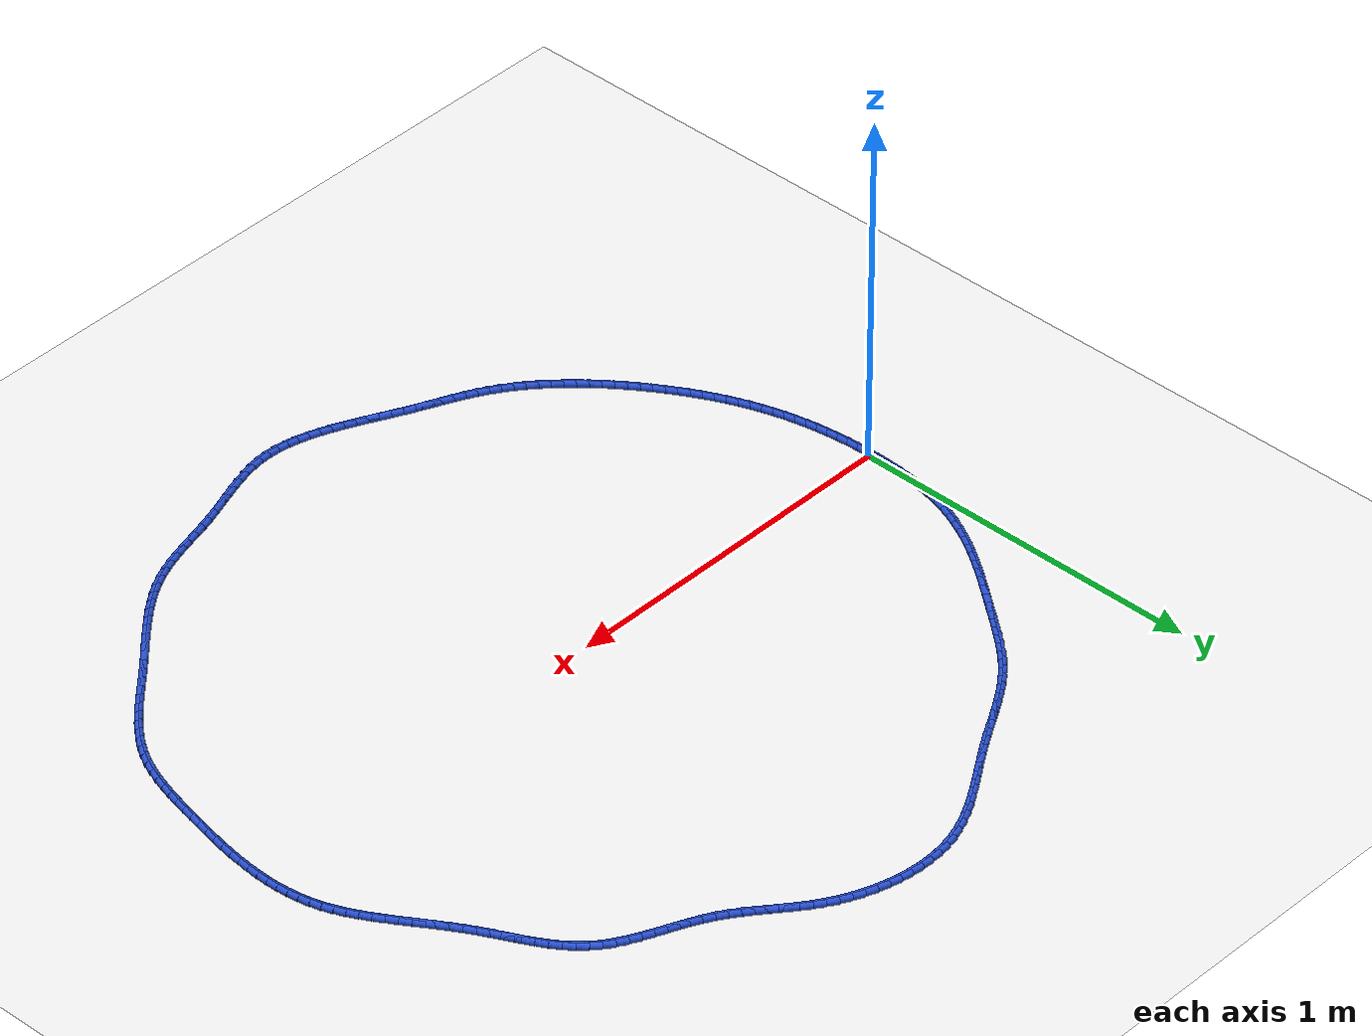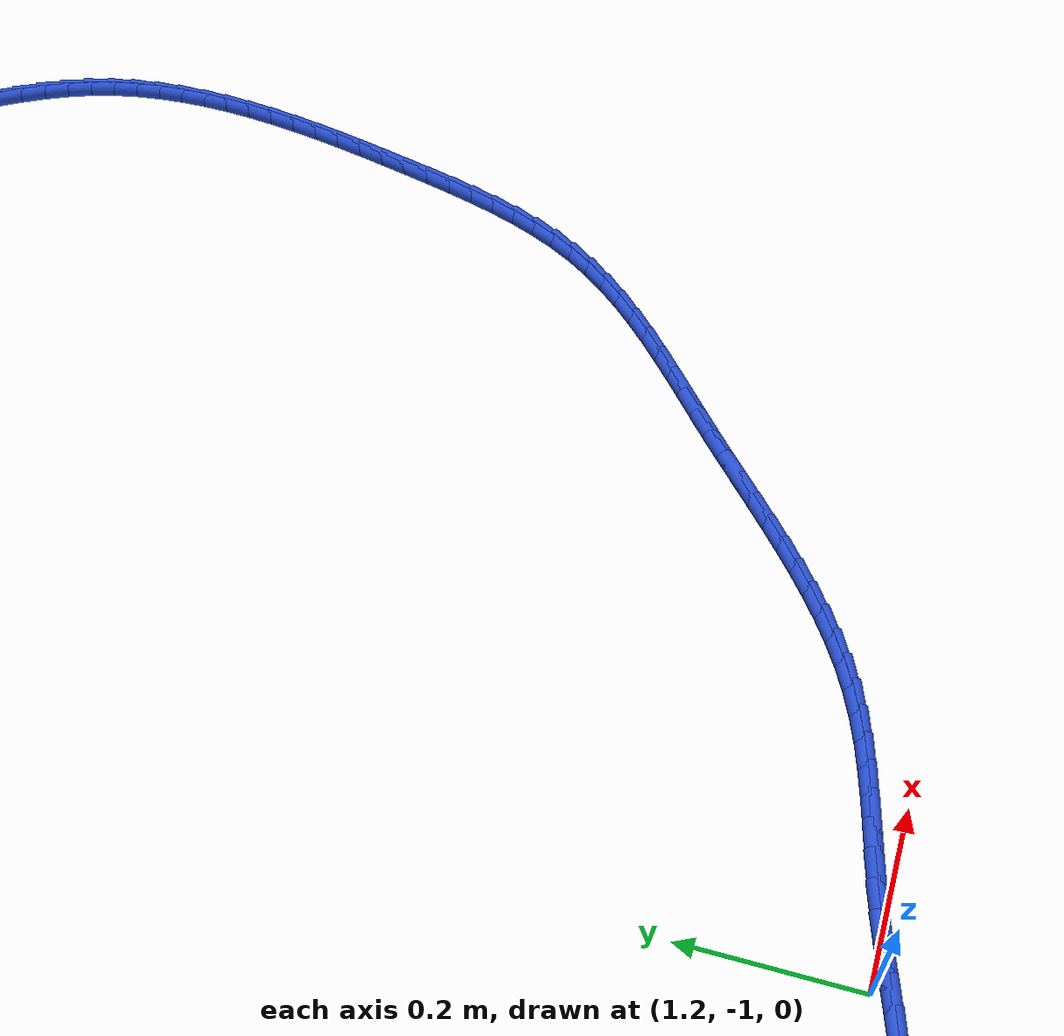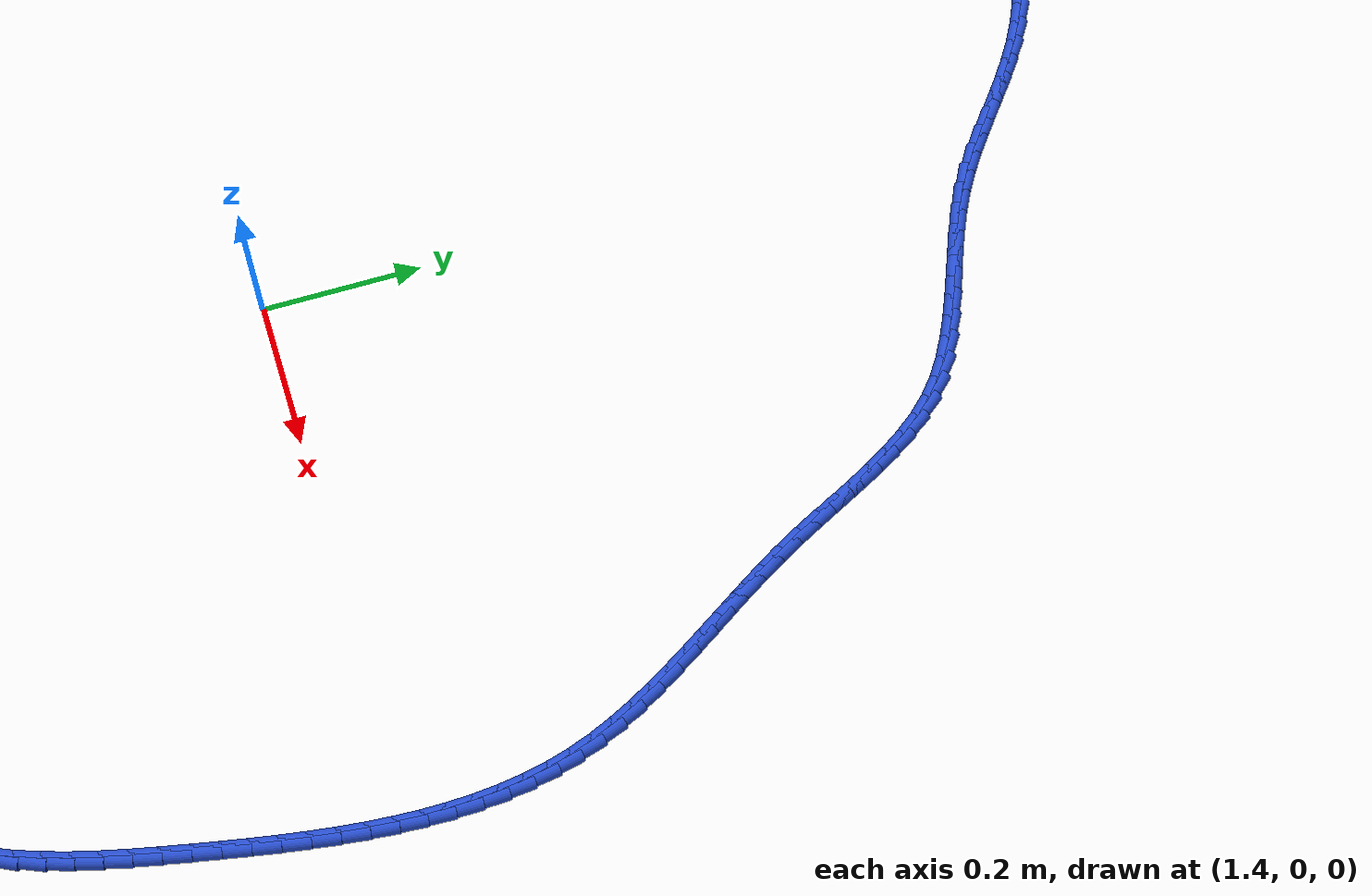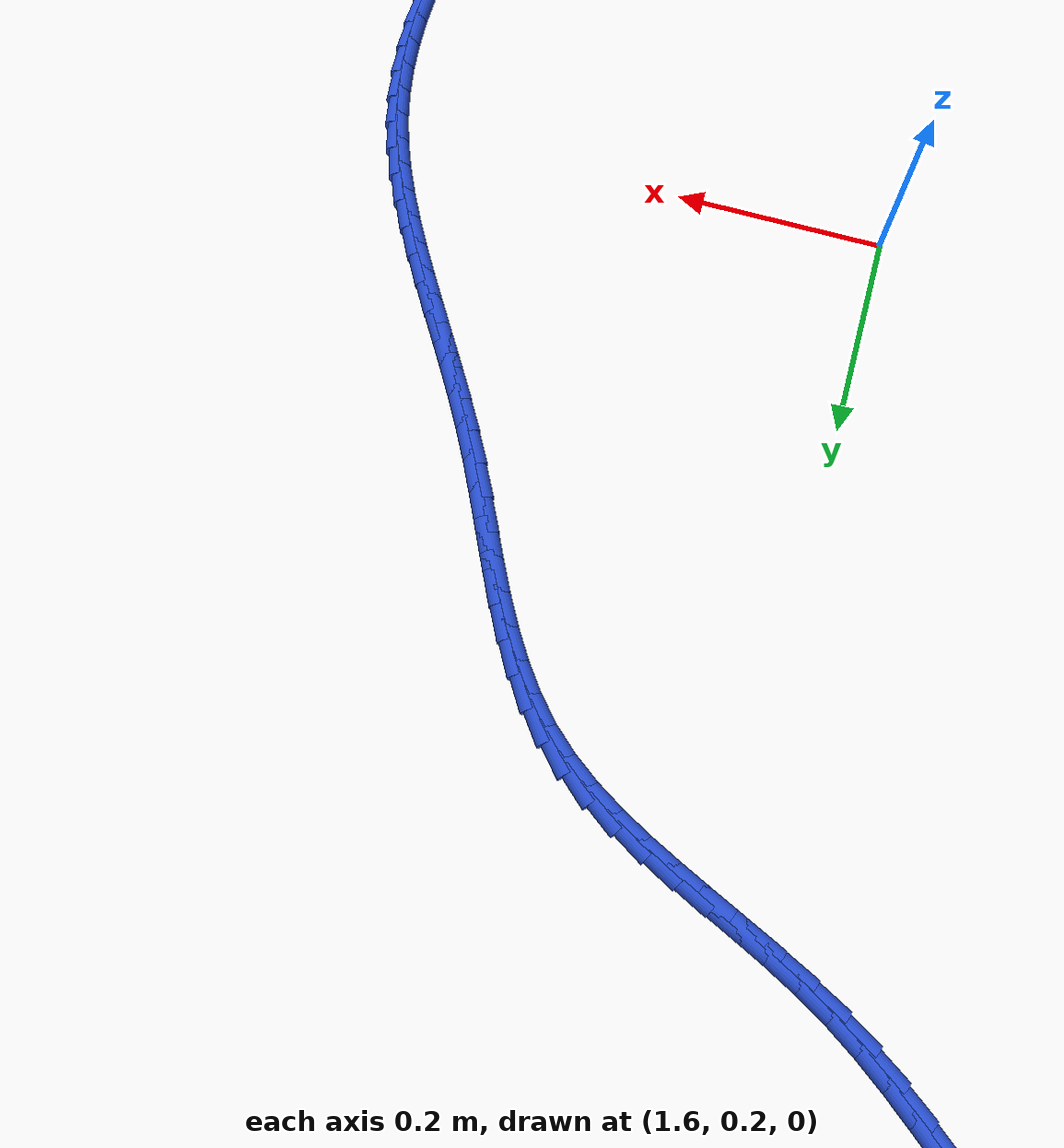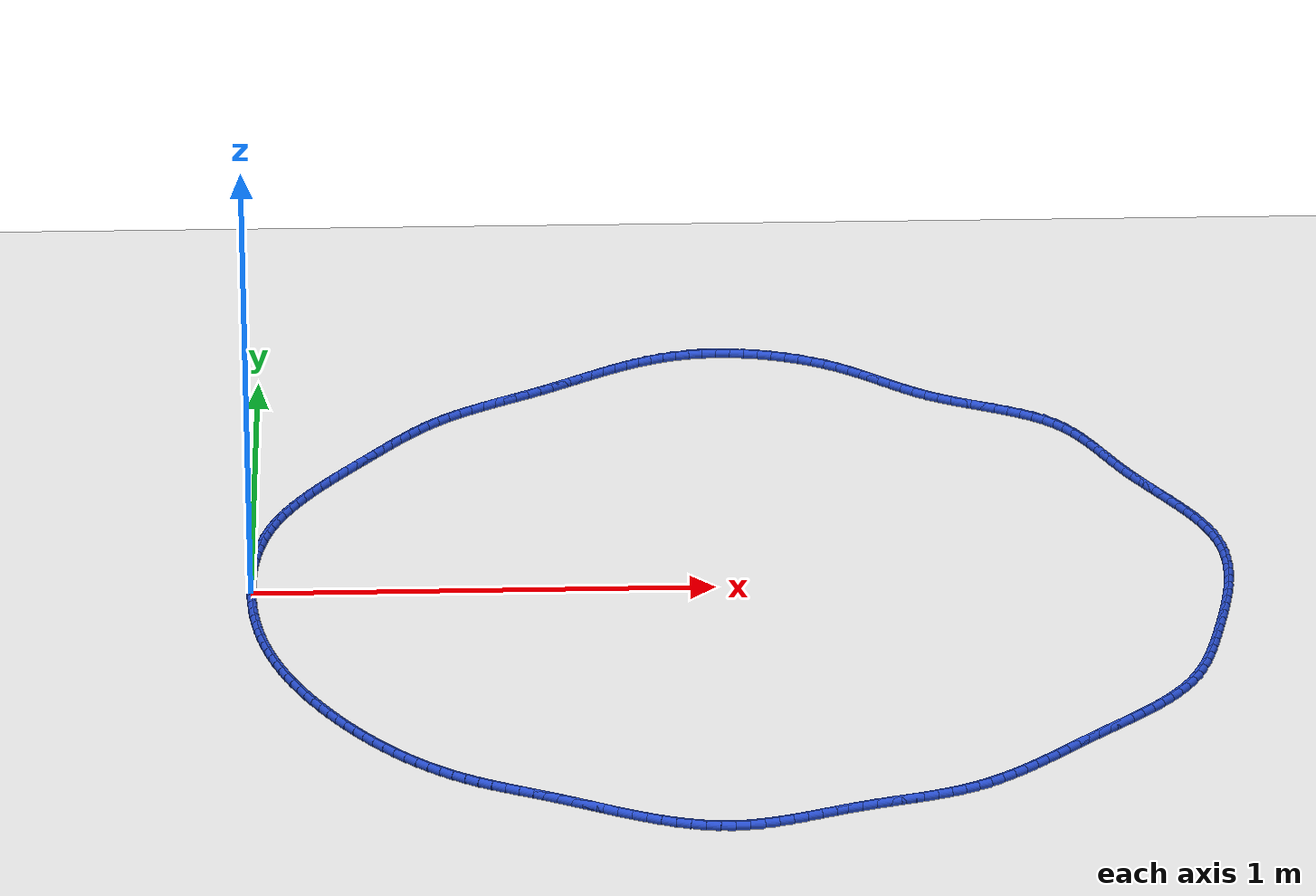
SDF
<sdf version="1.6">
 <world name="default">
  <light name="sun" type="directional">
   <pose>0 0 10 0 -0 0</pose>
   <diffuse>0.8 0.8 0.8 1</diffuse>
   <specular>0.2 0.2 0.2 1</specular>
   <attenuation>
    <range>1000</range>
    <constant>0.9</constant>
    <linear>0.01</linear>
    <quadratic>0.001</quadratic>
   </attenuation>
   <direction>-0.5 0.1 -0.9</direction>
  </light>
  <model name="ground_plane">
   <static>1</static>
   <link name="link">
    <collision name="collision">
     <geometry><plane><normal>0 0 1</normal><size>100 100</size></plane></geometry>
     <surface><friction><ode><mu>100</mu><mu2>50</mu2></ode></friction></surface>
    </collision>
    <visual name="visual">
     <cast_shadows>0</cast_shadows>
     <geometry><plane><normal>0 0 1</normal><size>100 100</size></plane></geometry>
     <material>
      <script><uri>file://media/materials/scripts/gazebo.material</uri><name>Gazebo/WhiteGlow</name></script>
     </material>
    </visual>
   </link>
  </model>
  <gravity>0 0 -9.8</gravity>
  <magnetic_field>6e-06 2.3e-05 -4.2e-05</magnetic_field>
  <atmosphere type="adiabatic"/>
  <physics name="default_physics" default="0" type="ode">
   <max_step_size>0.001</max_step_size>
   <real_time_factor>1</real_time_factor>
   <real_time_update_rate>1000</real_time_update_rate>
  </physics>
  <scene><ambient>0.4 0.4 0.4 1</ambient><background>0.7 0.7 0.7 1</background><shadows>1</shadows></scene>
  <spherical_coordinates>
   <surface_model>EARTH_WGS84</surface_model>
   <latitude_deg>0</latitude_deg>
   <longitude_deg>0</longitude_deg>
   <elevation>0</elevation>
   <heading_deg>0</heading_deg>
  </spherical_coordinates>
  <model name="line">
   <link name="link_0">
    <pose>-1.9949319973733282e-17 2.0816681711721685e-17 0.01 0 1.57 1.570620473035097</pose>
    <collision name="collision">
     <geometry><cylinder><radius>0.01</radius><length>0.08</length></cylinder></geometry>
    </collision>
    <visual name="visual">
     <material>
      <script><name>Gazebo/Blue</name><uri>file://media/materials/scripts/gazebo.material</uri></script>
     </material>
     <geometry><cylinder><radius>0.01</radius><length>0.08</length></cylinder></geometry>
    </visual>
   </link>
   <link name="link_1">
    <pose>5.557398307164433e-06 0.03160238516496424 0.01 0 1.57 1.5424077104782699</pose>
    <collision name="collision">
     <geometry><cylinder><radius>0.01</radius><length>0.08</length></cylinder></geometry>
    </collision>
    <visual name="visual">
     <material>
      <script><name>Gazebo/Blue</name><uri>file://media/materials/scripts/gazebo.material</uri></script>
     </material>
     <geometry><cylinder><radius>0.01</radius><length>0.08</length></cylinder></geometry>
    </visual>
   </link>
   <link name="link_2">
    <pose>0.0009031028297838526 0.06321027664661913 0.01 0 1.57 1.5117461191069241</pose>
    <collision name="collision">
     <geometry><cylinder><radius>0.01</radius><length>0.08</length></cylinder></geometry>
    </collision>
    <visual name="visual">
     <material>
      <script><name>Gazebo/Blue</name><uri>file://media/materials/scripts/gazebo.material</uri></script>
     </material>
     <geometry><cylinder><radius>0.01</radius><length>0.08</length></cylinder></geometry>
    </visual>
   </link>
   <link name="link_3">
    <pose>0.0027674546846880197 0.09474588796716679 0.01 0 1.57 1.478469907385745</pose>
    <collision name="collision">
     <geometry><cylinder><radius>0.01</radius><length>0.08</length></cylinder></geometry>
    </collision>
    <visual name="visual">
     <material>
      <script><name>Gazebo/Blue</name><uri>file://media/materials/scripts/gazebo.material</uri></script>
     </material>
     <geometry><cylinder><radius>0.01</radius><length>0.08</length></cylinder></geometry>
    </visual>
   </link>
   <link name="link_4">
    <pose>0.00567343135327765 0.12613143264880952 0.01 0 1.57 1.442407670167768</pose>
    <collision name="collision">
     <geometry><cylinder><radius>0.01</radius><length>0.08</length></cylinder></geometry>
    </collision>
    <visual name="visual">
     <material>
      <script><name>Gazebo/Blue</name><uri>file://media/materials/scripts/gazebo.material</uri></script>
     </material>
     <geometry><cylinder><radius>0.01</radius><length>0.08</length></cylinder></geometry>
    </visual>
   </link>
   <link name="link_5">
    <pose>0.009695851225810726 0.15728912421374944 0.01 0 1.57 1.403388178192306</pose>
    <collision name="collision">
     <geometry><cylinder><radius>0.01</radius><length>0.08</length></cylinder></geometry>
    </collision>
    <visual name="visual">
     <material>
      <script><name>Gazebo/Blue</name><uri>file://media/materials/scripts/gazebo.material</uri></script>
     </material>
     <geometry><cylinder><radius>0.01</radius><length>0.08</length></cylinder></geometry>
    </visual>
   </link>
   <link name="link_6">
    <pose>0.014909532692545226 0.18814117618418885 0.01 0 1.57 1.3612483226227403</pose>
    <collision name="collision">
     <geometry><cylinder><radius>0.01</radius><length>0.08</length></cylinder></geometry>
    </collision>
    <visual name="visual">
     <material>
      <script><name>Gazebo/Blue</name><uri>file://media/materials/scripts/gazebo.material</uri></script>
     </material>
     <geometry><cylinder><radius>0.01</radius><length>0.08</length></cylinder></geometry>
    </visual>
   </link>
   <link name="link_7">
    <pose>0.021389294143739135 0.21860980208232994 0.01 0 1.57 1.3158436273427838</pose>
    <collision name="collision">
     <geometry><cylinder><radius>0.01</radius><length>0.08</length></cylinder></geometry>
    </collision>
    <visual name="visual">
     <material>
      <script><name>Gazebo/Blue</name><uri>file://media/materials/scripts/gazebo.material</uri></script>
     </material>
     <geometry><cylinder><radius>0.01</radius><length>0.08</length></cylinder></geometry>
    </visual>
   </link>
   <link name="link_8">
    <pose>0.029209953969650426 0.24861721543037493 0.01 0 1.57 1.2670615961270724</pose>
    <collision name="collision">
     <geometry><cylinder><radius>0.01</radius><length>0.08</length></cylinder></geometry>
    </collision>
    <visual name="visual">
     <material>
      <script><name>Gazebo/Blue</name><uri>file://media/materials/scripts/gazebo.material</uri></script>
     </material>
     <geometry><cylinder><radius>0.01</radius><length>0.08</length></cylinder></geometry>
    </visual>
   </link>
   <link name="link_9">
    <pose>0.038446330560537076 0.27808562975052603 0.01 0 1.57 1.2149383889892116</pose>
    <collision name="collision">
     <geometry><cylinder><radius>0.01</radius><length>0.08</length></cylinder></geometry>
    </collision>
    <visual name="visual">
     <material>
      <script><name>Gazebo/Blue</name><uri>file://media/materials/scripts/gazebo.material</uri></script>
     </material>
     <geometry><cylinder><radius>0.01</radius><length>0.08</length></cylinder></geometry>
    </visual>
   </link>
   <link name="link_10">
    <pose>0.04917057625080608 0.3069389679852818 0.01 0 1.57 1.162907061438042</pose>
    <collision name="collision">
     <geometry><cylinder><radius>0.01</radius><length>0.08</length></cylinder></geometry>
    </collision>
    <visual name="visual">
     <material>
      <script><name>Gazebo/Blue</name><uri>file://media/materials/scripts/gazebo.material</uri></script>
     </material>
     <geometry><cylinder><radius>0.01</radius><length>0.08</length></cylinder></geometry>
    </visual>
   </link>
   <link name="link_11">
    <pose>0.06136502055713026 0.33515874562444475 0.01 0 1.57 1.1153209771724315</pose>
    <collision name="collision">
     <geometry><cylinder><radius>0.01</radius><length>0.08</length></cylinder></geometry>
    </collision>
    <visual name="visual">
     <material>
      <script><name>Gazebo/Blue</name><uri>file://media/materials/scripts/gazebo.material</uri></script>
     </material>
     <geometry><cylinder><radius>0.01</radius><length>0.08</length></cylinder></geometry>
    </visual>
   </link>
   <link name="link_12">
    <pose>0.07490272934567975 0.3627965357681093 0.01 0 1.57 1.0726076503873094</pose>
    <collision name="collision">
     <geometry><cylinder><radius>0.01</radius><length>0.08</length></cylinder></geometry>
    </collision>
    <visual name="visual">
     <material>
      <script><name>Gazebo/Blue</name><uri>file://media/materials/scripts/gazebo.material</uri></script>
     </material>
     <geometry><cylinder><radius>0.01</radius><length>0.08</length></cylinder></geometry>
    </visual>
   </link>
   <link name="link_13">
    <pose>0.08965016741289503 0.3899081439868075 0.01 0 1.57 1.0348352207601546</pose>
    <collision name="collision">
     <geometry><cylinder><radius>0.01</radius><length>0.08</length></cylinder></geometry>
    </collision>
    <visual name="visual">
     <material>
      <script><name>Gazebo/Blue</name><uri>file://media/materials/scripts/gazebo.material</uri></script>
     </material>
     <geometry><cylinder><radius>0.01</radius><length>0.08</length></cylinder></geometry>
    </visual>
   </link>
   <link name="link_14">
    <pose>0.10547379955521644 0.41654937585107144 0.01 0 1.57 1.001991078210965</pose>
    <collision name="collision">
     <geometry><cylinder><radius>0.01</radius><length>0.08</length></cylinder></geometry>
    </collision>
    <visual name="visual">
     <material>
      <script><name>Gazebo/Blue</name><uri>file://media/materials/scripts/gazebo.material</uri></script>
     </material>
     <geometry><cylinder><radius>0.01</radius><length>0.08</length></cylinder></geometry>
    </visual>
   </link>
   <link name="link_15">
    <pose>0.12224009056908439 0.442776036931433 0.01 0 1.57 0.9740098016397701</pose>
    <collision name="collision">
     <geometry><cylinder><radius>0.01</radius><length>0.08</length></cylinder></geometry>
    </collision>
    <visual name="visual">
     <material>
      <script><name>Gazebo/Blue</name><uri>file://media/materials/scripts/gazebo.material</uri></script>
     </material>
     <geometry><cylinder><radius>0.01</radius><length>0.08</length></cylinder></geometry>
    </visual>
   </link>
   <link name="link_16">
    <pose>0.13981550525093922 0.46864393279842426 0.01 0 1.57 0.9507972357020474</pose>
    <collision name="collision">
     <geometry><cylinder><radius>0.01</radius><length>0.08</length></cylinder></geometry>
    </collision>
    <visual name="visual">
     <material>
      <script><name>Gazebo/Blue</name><uri>file://media/materials/scripts/gazebo.material</uri></script>
     </material>
     <geometry><cylinder><radius>0.01</radius><length>0.08</length></cylinder></geometry>
    </visual>
   </link>
   <link name="link_17">
    <pose>0.15806650839722147 0.4942088690225771 0.01 0 1.57 0.9322499465729354</pose>
    <collision name="collision">
     <geometry><cylinder><radius>0.01</radius><length>0.08</length></cylinder></geometry>
    </collision>
    <visual name="visual">
     <material>
      <script><name>Gazebo/Blue</name><uri>file://media/materials/scripts/gazebo.material</uri></script>
     </material>
     <geometry><cylinder><radius>0.01</radius><length>0.08</length></cylinder></geometry>
    </visual>
   </link>
   <link name="link_18">
    <pose>0.17685956480437148 0.5195266511744236 0.01 0 1.57 0.9182701466582173</pose>
    <collision name="collision">
     <geometry><cylinder><radius>0.01</radius><length>0.08</length></cylinder></geometry>
    </collision>
    <visual name="visual">
     <material>
      <script><name>Gazebo/Blue</name><uri>file://media/materials/scripts/gazebo.material</uri></script>
     </material>
     <geometry><cylinder><radius>0.01</radius><length>0.08</length></cylinder></geometry>
    </visual>
   </link>
   <link name="link_19">
    <pose>0.19606113926882968 0.5446530848244959 0.01 0 1.57 0.9087766129086358</pose>
    <collision name="collision">
     <geometry><cylinder><radius>0.01</radius><length>0.08</length></cylinder></geometry>
    </collision>
    <visual name="visual">
     <material>
      <script><name>Gazebo/Blue</name><uri>file://media/materials/scripts/gazebo.material</uri></script>
     </material>
     <geometry><cylinder><radius>0.01</radius><length>0.08</length></cylinder></geometry>
    </visual>
   </link>
   <link name="link_20">
    <pose>0.2155376965870364 0.5696439755433259 0.01 0 1.57 0.9037122587128621</pose>
    <collision name="collision">
     <geometry><cylinder><radius>0.01</radius><length>0.08</length></cylinder></geometry>
    </collision>
    <visual name="visual">
     <material>
      <script><name>Gazebo/Blue</name><uri>file://media/materials/scripts/gazebo.material</uri></script>
     </material>
     <geometry><cylinder><radius>0.01</radius><length>0.08</length></cylinder></geometry>
    </visual>
   </link>
   <link name="link_21">
    <pose>0.235155701555432 0.5945551289014454 0.01 0 1.57 0.9030418218896888</pose>
    <collision name="collision">
     <geometry><cylinder><radius>0.01</radius><length>0.08</length></cylinder></geometry>
    </collision>
    <visual name="visual">
     <material>
      <script><name>Gazebo/Blue</name><uri>file://media/materials/scripts/gazebo.material</uri></script>
     </material>
     <geometry><cylinder><radius>0.01</radius><length>0.08</length></cylinder></geometry>
    </visual>
   </link>
   <link name="link_22">
    <pose>0.25478179350809294 0.6194422060765593 0.01 0 1.57 0.9036620928028535</pose>
    <collision name="collision">
     <geometry><cylinder><radius>0.01</radius><length>0.08</length></cylinder></geometry>
    </collision>
    <visual name="visual">
     <material>
      <script><name>Gazebo/Blue</name><uri>file://media/materials/scripts/gazebo.material</uri></script>
     </material>
     <geometry><cylinder><radius>0.01</radius><length>0.08</length></cylinder></geometry>
    </visual>
   </link>
   <link name="link_23">
    <pose>0.27435837320930523 0.6442981917522731 0.01 0 1.57 0.8976073200366024</pose>
    <collision name="collision">
     <geometry><cylinder><radius>0.01</radius><length>0.08</length></cylinder></geometry>
    </collision>
    <visual name="visual">
     <material>
      <script><name>Gazebo/Blue</name><uri>file://media/materials/scripts/gazebo.material</uri></script>
     </material>
     <geometry><cylinder><radius>0.01</radius><length>0.08</length></cylinder></geometry>
    </visual>
   </link>
   <link name="link_24">
    <pose>0.29402169698010006 0.6689556963079493 0.01 0 1.57 0.8835233571242196</pose>
    <collision name="collision">
     <geometry><cylinder><radius>0.01</radius><length>0.08</length></cylinder></geometry>
    </collision>
    <visual name="visual">
     <material>
      <script><name>Gazebo/Blue</name><uri>file://media/materials/scripts/gazebo.material</uri></script>
     </material>
     <geometry><cylinder><radius>0.01</radius><length>0.08</length></cylinder></geometry>
    </visual>
   </link>
   <link name="link_25">
    <pose>0.313938586843094 0.6932220434961034 0.01 0 1.57 0.8612462771705812</pose>
    <collision name="collision">
     <geometry><cylinder><radius>0.01</radius><length>0.08</length></cylinder></geometry>
    </collision>
    <visual name="visual">
     <material>
      <script><name>Gazebo/Blue</name><uri>file://media/materials/scripts/gazebo.material</uri></script>
     </material>
     <geometry><cylinder><radius>0.01</radius><length>0.08</length></cylinder></geometry>
    </visual>
   </link>
   <link name="link_26">
    <pose>0.3342758648209037 0.7169045570692514 0.01 0 1.57 0.8305760113585051</pose>
    <collision name="collision">
     <geometry><cylinder><radius>0.01</radius><length>0.08</length></cylinder></geometry>
    </collision>
    <visual name="visual">
     <material>
      <script><name>Gazebo/Blue</name><uri>file://media/materials/scripts/gazebo.material</uri></script>
     </material>
     <geometry><cylinder><radius>0.01</radius><length>0.08</length></cylinder></geometry>
    </visual>
   </link>
   <link name="link_27">
    <pose>0.3552003529361461 0.7398105607799093 0.01 0 1.57 0.7913202614106805</pose>
    <collision name="collision">
     <geometry><cylinder><radius>0.01</radius><length>0.08</length></cylinder></geometry>
    </collision>
    <visual name="visual">
     <material>
      <script><name>Gazebo/Blue</name><uri>file://media/materials/scripts/gazebo.material</uri></script>
     </material>
     <geometry><cylinder><radius>0.01</radius><length>0.08</length></cylinder></geometry>
    </visual>
   </link>
   <link name="link_28">
    <pose>0.3768788732114375 0.7617473783805924 0.01 0 1.57 0.7433607548576796</pose>
    <collision name="collision">
     <geometry><cylinder><radius>0.01</radius><length>0.08</length></cylinder></geometry>
    </collision>
    <visual name="visual">
     <material>
      <script><name>Gazebo/Blue</name><uri>file://media/materials/scripts/gazebo.material</uri></script>
     </material>
     <geometry><cylinder><radius>0.01</radius><length>0.08</length></cylinder></geometry>
    </visual>
   </link>
   <link name="link_29">
    <pose>0.3994782476693945 0.7825223336238171 0.01 0 1.57 0.6880846830388176</pose>
    <collision name="collision">
     <geometry><cylinder><radius>0.01</radius><length>0.08</length></cylinder></geometry>
    </collision>
    <visual name="visual">
     <material>
      <script><name>Gazebo/Blue</name><uri>file://media/materials/scripts/gazebo.material</uri></script>
     </material>
     <geometry><cylinder><radius>0.01</radius><length>0.08</length></cylinder></geometry>
    </visual>
   </link>
   <link name="link_30">
    <pose>0.423140295860783 0.8019754048748649 0.01 0 1.57 0.6365788960101656</pose>
    <collision name="collision">
     <geometry><cylinder><radius>0.01</radius><length>0.08</length></cylinder></geometry>
    </collision>
    <visual name="visual">
     <material>
      <script><name>Gazebo/Blue</name><uri>file://media/materials/scripts/gazebo.material</uri></script>
     </material>
     <geometry><cylinder><radius>0.01</radius><length>0.08</length></cylinder></geometry>
    </visual>
   </link>
   <link name="link_31">
    <pose>0.4478058052764403 0.8202091295015653 0.01 0 1.57 0.5943485693807677</pose>
    <collision name="collision">
     <geometry><cylinder><radius>0.01</radius><length>0.08</length></cylinder></geometry>
    </collision>
    <visual name="visual">
     <material>
      <script><name>Gazebo/Blue</name><uri>file://media/materials/scripts/gazebo.material</uri></script>
     </material>
     <geometry><cylinder><radius>0.01</radius><length>0.08</length></cylinder></geometry>
    </visual>
   </link>
   <link name="link_32">
    <pose>0.4733186847800422 0.8374525737235404 0.01 0 1.57 0.5614984114020866</pose>
    <collision name="collision">
     <geometry><cylinder><radius>0.01</radius><length>0.08</length></cylinder></geometry>
    </collision>
    <visual name="visual">
     <material>
      <script><name>Gazebo/Blue</name><uri>file://media/materials/scripts/gazebo.material</uri></script>
     </material>
     <geometry><cylinder><radius>0.01</radius><length>0.08</length></cylinder></geometry>
    </visual>
   </link>
   <link name="link_33">
    <pose>0.49952222074395985 0.8539356167685246 0.01 0 1.57 0.5379417118628834</pose>
    <collision name="collision">
     <geometry><cylinder><radius>0.01</radius><length>0.08</length></cylinder></geometry>
    </collision>
    <visual name="visual">
     <material>
      <script><name>Gazebo/Blue</name><uri>file://media/materials/scripts/gazebo.material</uri></script>
     </material>
     <geometry><cylinder><radius>0.01</radius><length>0.08</length></cylinder></geometry>
    </visual>
   </link>
   <link name="link_34">
    <pose>0.5262596995405647 0.8698881378642535 0.01 0 1.57 0.5235211687718093</pose>
    <collision name="collision">
     <geometry><cylinder><radius>0.01</radius><length>0.08</length></cylinder></geometry>
    </collision>
    <visual name="visual">
     <material>
      <script><name>Gazebo/Blue</name><uri>file://media/materials/scripts/gazebo.material</uri></script>
     </material>
     <geometry><cylinder><radius>0.01</radius><length>0.08</length></cylinder></geometry>
    </visual>
   </link>
   <link name="link_35">
    <pose>0.5533744075422284 0.8855400162384623 0.01 0 1.57 0.5180695622502376</pose>
    <collision name="collision">
     <geometry><cylinder><radius>0.01</radius><length>0.08</length></cylinder></geometry>
    </collision>
    <visual name="visual">
     <material>
      <script><name>Gazebo/Blue</name><uri>file://media/materials/scripts/gazebo.material</uri></script>
     </material>
     <geometry><cylinder><radius>0.01</radius><length>0.08</length></cylinder></geometry>
    </visual>
   </link>
   <link name="link_36">
    <pose>0.580709631121322 0.9011211311188863 0.01 0 1.57 0.5214444527282545</pose>
    <collision name="collision">
     <geometry><cylinder><radius>0.01</radius><length>0.08</length></cylinder></geometry>
    </collision>
    <visual name="visual">
     <material>
      <script><name>Gazebo/Blue</name><uri>file://media/materials/scripts/gazebo.material</uri></script>
     </material>
     <geometry><cylinder><radius>0.01</radius><length>0.08</length></cylinder></geometry>
    </visual>
   </link>
   <link name="link_37">
    <pose>0.6081086566502177 0.9168613617332605 0.01 0 1.57 0.533539737842028</pose>
    <collision name="collision">
     <geometry><cylinder><radius>0.01</radius><length>0.08</length></cylinder></geometry>
    </collision>
    <visual name="visual">
     <material>
      <script><name>Gazebo/Blue</name><uri>file://media/materials/scripts/gazebo.material</uri></script>
     </material>
     <geometry><cylinder><radius>0.01</radius><length>0.08</length></cylinder></geometry>
    </visual>
   </link>
   <link name="link_38">
    <pose>0.6354147705012866 0.9329905873093206 0.01 0 1.57 0.5530765222836852</pose>
    <collision name="collision">
     <geometry><cylinder><radius>0.01</radius><length>0.08</length></cylinder></geometry>
    </collision>
    <visual name="visual">
     <material>
      <script><name>Gazebo/Blue</name><uri>file://media/materials/scripts/gazebo.material</uri></script>
     </material>
     <geometry><cylinder><radius>0.01</radius><length>0.08</length></cylinder></geometry>
    </visual>
   </link>
   <link name="link_39">
    <pose>0.6624883467744029 0.9497043569322907 0.01 0 1.57 0.5691643577340945</pose>
    <collision name="collision">
     <geometry><cylinder><radius>0.01</radius><length>0.08</length></cylinder></geometry>
    </collision>
    <visual name="visual">
     <material>
      <script><name>Gazebo/Blue</name><uri>file://media/materials/scripts/gazebo.material</uri></script>
     </material>
     <geometry><cylinder><radius>0.01</radius><length>0.08</length></cylinder></geometry>
    </visual>
   </link>
   <link name="link_40">
    <pose>0.6893447555070588 0.9668868247037277 0.01 0 1.57 0.5761210144276192</pose>
    <collision name="collision">
     <geometry><cylinder><radius>0.01</radius><length>0.08</length></cylinder></geometry>
    </collision>
    <visual name="visual">
     <material>
      <script><name>Gazebo/Blue</name><uri>file://media/materials/scripts/gazebo.material</uri></script>
     </material>
     <geometry><cylinder><radius>0.01</radius><length>0.08</length></cylinder></geometry>
    </visual>
   </link>
   <link name="link_41">
    <pose>0.7160819109879252 0.9842563089868874 0.01 0 1.57 0.5739373194317391</pose>
    <collision name="collision">
     <geometry><cylinder><radius>0.01</radius><length>0.08</length></cylinder></geometry>
    </collision>
    <visual name="visual">
     <material>
      <script><name>Gazebo/Blue</name><uri>file://media/materials/scripts/gazebo.material</uri></script>
     </material>
     <geometry><cylinder><radius>0.01</radius><length>0.08</length></cylinder></geometry>
    </visual>
   </link>
   <link name="link_42">
    <pose>0.7427984957673237 1.0015295846669987 0.01 0 1.57 0.5625388767694409</pose>
    <collision name="collision">
     <geometry><cylinder><radius>0.01</radius><length>0.08</length></cylinder></geometry>
    </collision>
    <visual name="visual">
     <material>
      <script><name>Gazebo/Blue</name><uri>file://media/materials/scripts/gazebo.material</uri></script>
     </material>
     <geometry><cylinder><radius>0.01</radius><length>0.08</length></cylinder></geometry>
    </visual>
   </link>
   <link name="link_43">
    <pose>0.769593192395576 1.01842342662929 0.01 0 1.57 0.5417348971957683</pose>
    <collision name="collision">
     <geometry><cylinder><radius>0.01</radius><length>0.08</length></cylinder></geometry>
    </collision>
    <visual name="visual">
     <material>
      <script><name>Gazebo/Blue</name><uri>file://media/materials/scripts/gazebo.material</uri></script>
     </material>
     <geometry><cylinder><radius>0.01</radius><length>0.08</length></cylinder></geometry>
    </visual>
   </link>
   <link name="link_44">
    <pose>0.7965646834230035 1.0346546097589908 0.01 0 1.57 0.5112422892850454</pose>
    <collision name="collision">
     <geometry><cylinder><radius>0.01</radius><length>0.08</length></cylinder></geometry>
    </collision>
    <visual name="visual">
     <material>
      <script><name>Gazebo/Blue</name><uri>file://media/materials/scripts/gazebo.material</uri></script>
     </material>
     <geometry><cylinder><radius>0.01</radius><length>0.08</length></cylinder></geometry>
    </visual>
   </link>
   <link name="link_45">
    <pose>0.8238116513999274 1.0499399089413295 0.01 0 1.57 0.4707364337846891</pose>
    <collision name="collision">
     <geometry><cylinder><radius>0.01</radius><length>0.08</length></cylinder></geometry>
    </collision>
    <visual name="visual">
     <material>
      <script><name>Gazebo/Blue</name><uri>file://media/materials/scripts/gazebo.material</uri></script>
     </material>
     <geometry><cylinder><radius>0.01</radius><length>0.08</length></cylinder></geometry>
    </visual>
   </link>
   <link name="link_46">
    <pose>0.8514327788766696 1.0639960990615354 0.01 0 1.57 0.41993650338634947</pose>
    <collision name="collision">
     <geometry><cylinder><radius>0.01</radius><length>0.08</length></cylinder></geometry>
    </collision>
    <visual name="visual">
     <material>
      <script><name>Gazebo/Blue</name><uri>file://media/materials/scripts/gazebo.material</uri></script>
     </material>
     <geometry><cylinder><radius>0.01</radius><length>0.08</length></cylinder></geometry>
    </visual>
   </link>
   <link name="link_47">
    <pose>0.8795267484035513 1.0765399550048371 0.01 0 1.57 0.3587320220550655</pose>
    <collision name="collision">
     <geometry><cylinder><radius>0.01</radius><length>0.08</length></cylinder></geometry>
    </collision>
    <visual name="visual">
     <material>
      <script><name>Gazebo/Blue</name><uri>file://media/materials/scripts/gazebo.material</uri></script>
     </material>
     <geometry><cylinder><radius>0.01</radius><length>0.08</length></cylinder></geometry>
    </visual>
   </link>
   <link name="link_48">
    <pose>0.9081922425308943 1.0872882516564635 0.01 0 1.57 0.28734873083687706</pose>
    <collision name="collision">
     <geometry><cylinder><radius>0.01</radius><length>0.08</length></cylinder></geometry>
    </collision>
    <visual name="visual">
     <material>
      <script><name>Gazebo/Blue</name><uri>file://media/materials/scripts/gazebo.material</uri></script>
     </material>
     <geometry><cylinder><radius>0.01</radius><length>0.08</length></cylinder></geometry>
    </visual>
   </link>
   <link name="link_49">
    <pose>0.9375279438090196 1.0959577639016433 0.01 0 1.57 0.2069095050335091</pose>
    <collision name="collision">
     <geometry><cylinder><radius>0.01</radius><length>0.08</length></cylinder></geometry>
    </collision>
    <visual name="visual">
     <material>
      <script><name>Gazebo/Blue</name><uri>file://media/materials/scripts/gazebo.material</uri></script>
     </material>
     <geometry><cylinder><radius>0.01</radius><length>0.08</length></cylinder></geometry>
    </visual>
   </link>
   <link name="link_50">
    <pose>0.9676244748101472 1.102275437049532 0.01 0 1.57 0.1253019849651596</pose>
    <collision name="collision">
     <geometry><cylinder><radius>0.01</radius><length>0.08</length></cylinder></geometry>
    </collision>
    <visual name="visual">
     <material>
      <script><name>Gazebo/Blue</name><uri>file://media/materials/scripts/gazebo.material</uri></script>
     </material>
     <geometry><cylinder><radius>0.01</radius><length>0.08</length></cylinder></geometry>
    </visual>
   </link>
   <link name="link_51">
    <pose>0.9984243915354494 1.106155053119983 0.01 0 1.57 0.04847560307408553</pose>
    <collision name="collision">
     <geometry><cylinder><radius>0.01</radius><length>0.08</length></cylinder></geometry>
    </collision>
    <visual name="visual">
     <material>
      <script><name>Gazebo/Blue</name><uri>file://media/materials/scripts/gazebo.material</uri></script>
     </material>
     <geometry><cylinder><radius>0.01</radius><length>0.08</length></cylinder></geometry>
    </visual>
   </link>
   <link name="link_52">
    <pose>1.0297403531845026 1.1076743034539662 0.01 0 1.57 -0.023947935337501752</pose>
    <collision name="collision">
     <geometry><cylinder><radius>0.01</radius><length>0.08</length></cylinder></geometry>
    </collision>
    <visual name="visual">
     <material>
      <script><name>Gazebo/Blue</name><uri>file://media/materials/scripts/gazebo.material</uri></script>
     </material>
     <geometry><cylinder><radius>0.01</radius><length>0.08</length></cylinder></geometry>
    </visual>
   </link>
   <link name="link_53">
    <pose>1.0613806124697045 1.1069164396858013 0.01 0 1.57 -0.09263512583752934</pose>
    <collision name="collision">
     <geometry><cylinder><radius>0.01</radius><length>0.08</length></cylinder></geometry>
    </collision>
    <visual name="visual">
     <material>
      <script><name>Gazebo/Blue</name><uri>file://media/materials/scripts/gazebo.material</uri></script>
     </material>
     <geometry><cylinder><radius>0.01</radius><length>0.08</length></cylinder></geometry>
    </visual>
   </link>
   <link name="link_54">
    <pose>1.093153422103452 1.103964713449809 0.01 0 1.57 -0.15829118914416004</pose>
    <collision name="collision">
     <geometry><cylinder><radius>0.01</radius><length>0.08</length></cylinder></geometry>
    </collision>
    <visual name="visual">
     <material>
      <script><name>Gazebo/Blue</name><uri>file://media/materials/scripts/gazebo.material</uri></script>
     </material>
     <geometry><cylinder><radius>0.01</radius><length>0.08</length></cylinder></geometry>
    </visual>
   </link>
   <link name="link_55">
    <pose>1.124867034798142 1.0989023763803092 0.01 0 1.57 -0.22163496721484707</pose>
    <collision name="collision">
     <geometry><cylinder><radius>0.01</radius><length>0.08</length></cylinder></geometry>
    </collision>
    <visual name="visual">
     <material>
      <script><name>Gazebo/Blue</name><uri>file://media/materials/scripts/gazebo.material</uri></script>
     </material>
     <geometry><cylinder><radius>0.01</radius><length>0.08</length></cylinder></geometry>
    </visual>
   </link>
   <link name="link_56">
    <pose>1.1563297032661723 1.091812680111622 0.01 0 1.57 -0.2833873491306156</pose>
    <collision name="collision">
     <geometry><cylinder><radius>0.01</radius><length>0.08</length></cylinder></geometry>
    </collision>
    <visual name="visual">
     <material>
      <script><name>Gazebo/Blue</name><uri>file://media/materials/scripts/gazebo.material</uri></script>
     </material>
     <geometry><cylinder><radius>0.01</radius><length>0.08</length></cylinder></geometry>
    </visual>
   </link>
   <link name="link_57">
    <pose>1.1873496802199381 1.0827788762780668 0.01 0 1.57 -0.34426916223466975</pose>
    <collision name="collision">
     <geometry><cylinder><radius>0.01</radius><length>0.08</length></cylinder></geometry>
    </collision>
    <visual name="visual">
     <material>
      <script><name>Gazebo/Blue</name><uri>file://media/materials/scripts/gazebo.material</uri></script>
     </material>
     <geometry><cylinder><radius>0.01</radius><length>0.08</length></cylinder></geometry>
    </visual>
   </link>
   <link name="link_58">
    <pose>1.2177352183718386 1.0718842165139653 0.01 0 1.57 -0.40500525535311727</pose>
    <collision name="collision">
     <geometry><cylinder><radius>0.01</radius><length>0.08</length></cylinder></geometry>
    </collision>
    <visual name="visual">
     <material>
      <script><name>Gazebo/Blue</name><uri>file://media/materials/scripts/gazebo.material</uri></script>
     </material>
     <geometry><cylinder><radius>0.01</radius><length>0.08</length></cylinder></geometry>
    </visual>
   </link>
   <link name="link_59">
    <pose>1.2472945704342693 1.0592119524536365 0.01 0 1.57 -0.4663322243100996</pose>
    <collision name="collision">
     <geometry><cylinder><radius>0.01</radius><length>0.08</length></cylinder></geometry>
    </collision>
    <visual name="visual">
     <material>
      <script><name>Gazebo/Blue</name><uri>file://media/materials/scripts/gazebo.material</uri></script>
     </material>
     <geometry><cylinder><radius>0.01</radius><length>0.08</length></cylinder></geometry>
    </visual>
   </link>
   <link name="link_60">
    <pose>1.2758359891196285 1.044845335731401 0.01 0 1.57 -0.5289509135889633</pose>
    <collision name="collision">
     <geometry><cylinder><radius>0.01</radius><length>0.08</length></cylinder></geometry>
    </collision>
    <visual name="visual">
     <material>
      <script><name>Gazebo/Blue</name><uri>file://media/materials/scripts/gazebo.material</uri></script>
     </material>
     <geometry><cylinder><radius>0.01</radius><length>0.08</length></cylinder></geometry>
    </visual>
   </link>
   <link name="link_61">
    <pose>1.3031695011801545 1.028868661734508 0.01 0 1.57 -0.5879392882483317</pose>
    <collision name="collision">
     <geometry><cylinder><radius>0.01</radius><length>0.08</length></cylinder></geometry>
    </collision>
    <visual name="visual">
     <material>
      <script><name>Gazebo/Blue</name><uri>file://media/materials/scripts/gazebo.material</uri></script>
     </material>
     <geometry><cylinder><radius>0.01</radius><length>0.08</length></cylinder></geometry>
    </visual>
   </link>
   <link name="link_62">
    <pose>1.3292759695310825 1.0114667369781303 0.01 0 1.57 -0.6327775586561226</pose>
    <collision name="collision">
     <geometry><cylinder><radius>0.01</radius><length>0.08</length></cylinder></geometry>
    </collision>
    <visual name="visual">
     <material>
      <script><name>Gazebo/Blue</name><uri>file://media/materials/scripts/gazebo.material</uri></script>
     </material>
     <geometry><cylinder><radius>0.01</radius><length>0.08</length></cylinder></geometry>
    </visual>
   </link>
   <link name="link_63">
    <pose>1.3544467552334647 0.9930070489643389 0.01 0 1.57 -0.6617763972199897</pose>
    <collision name="collision">
     <geometry><cylinder><radius>0.01</radius><length>0.08</length></cylinder></geometry>
    </collision>
    <visual name="visual">
     <material>
      <script><name>Gazebo/Blue</name><uri>file://media/materials/scripts/gazebo.material</uri></script>
     </material>
     <geometry><cylinder><radius>0.01</radius><length>0.08</length></cylinder></geometry>
    </visual>
   </link>
   <link name="link_64">
    <pose>1.379006091449195 0.9738764254325137 0.01 0 1.57 -0.6746664620363154</pose>
    <collision name="collision">
     <geometry><cylinder><radius>0.01</radius><length>0.08</length></cylinder></geometry>
    </collision>
    <visual name="visual">
     <material>
      <script><name>Gazebo/Blue</name><uri>file://media/materials/scripts/gazebo.material</uri></script>
     </material>
     <geometry><cylinder><radius>0.01</radius><length>0.08</length></cylinder></geometry>
    </visual>
   </link>
   <link name="link_65">
    <pose>1.4032782113401683 0.9544616941220333 0.01 0 1.57 -0.6713379799891075</pose>
    <collision name="collision">
     <geometry><cylinder><radius>0.01</radius><length>0.08</length></cylinder></geometry>
    </collision>
    <visual name="visual">
     <material>
      <script><name>Gazebo/Blue</name><uri>file://media/materials/scripts/gazebo.material</uri></script>
     </material>
     <geometry><cylinder><radius>0.01</radius><length>0.08</length></cylinder></geometry>
    </visual>
   </link>
   <link name="link_66">
    <pose>1.427587348068279 0.9351496827722756 0.01 0 1.57 -0.6517426442098071</pose>
    <collision name="collision">
     <geometry><cylinder><radius>0.01</radius><length>0.08</length></cylinder></geometry>
    </collision>
    <visual name="visual">
     <material>
      <script><name>Gazebo/Blue</name><uri>file://media/materials/scripts/gazebo.material</uri></script>
     </material>
     <geometry><cylinder><radius>0.01</radius><length>0.08</length></cylinder></geometry>
    </visual>
   </link>
   <link name="link_67">
    <pose>1.4522577347954202 0.9163272191226197 0.01 0 1.57 -0.6159207751072725</pose>
    <collision name="collision">
     <geometry><cylinder><radius>0.01</radius><length>0.08</length></cylinder></geometry>
    </collision>
    <visual name="visual">
     <material>
      <script><name>Gazebo/Blue</name><uri>file://media/materials/scripts/gazebo.material</uri></script>
     </material>
     <geometry><cylinder><radius>0.01</radius><length>0.08</length></cylinder></geometry>
    </visual>
   </link>
   <link name="link_68">
    <pose>1.477613604683487 0.8983811309124442 0.01 0 1.57 -0.5641545823564459</pose>
    <collision name="collision">
     <geometry><cylinder><radius>0.01</radius><length>0.08</length></cylinder></geometry>
    </collision>
    <visual name="visual">
     <material>
      <script><name>Gazebo/Blue</name><uri>file://media/materials/scripts/gazebo.material</uri></script>
     </material>
     <geometry><cylinder><radius>0.01</radius><length>0.08</length></cylinder></geometry>
    </visual>
   </link>
   <link name="link_69">
    <pose>1.5039791908943738 0.8816982458811271 0.01 0 1.57 -0.5023420362251353</pose>
    <collision name="collision">
     <geometry><cylinder><radius>0.01</radius><length>0.08</length></cylinder></geometry>
    </collision>
    <visual name="visual">
     <material>
      <script><name>Gazebo/Blue</name><uri>file://media/materials/scripts/gazebo.material</uri></script>
     </material>
     <geometry><cylinder><radius>0.01</radius><length>0.08</length></cylinder></geometry>
    </visual>
   </link>
   <link name="link_70">
    <pose>1.5315708380627264 0.8665408462534969 0.01 0 1.57 -0.4533530131407078</pose>
    <collision name="collision">
     <geometry><cylinder><radius>0.01</radius><length>0.08</length></cylinder></geometry>
    </collision>
    <visual name="visual">
     <material>
      <script><name>Gazebo/Blue</name><uri>file://media/materials/scripts/gazebo.material</uri></script>
     </material>
     <geometry><cylinder><radius>0.01</radius><length>0.08</length></cylinder></geometry>
    </visual>
   </link>
   <link name="link_71">
    <pose>1.5601323743781133 0.8526257456555674 0.01 0 1.57 -0.4225574086660792</pose>
    <collision name="collision">
     <geometry><cylinder><radius>0.01</radius><length>0.08</length></cylinder></geometry>
    </collision>
    <visual name="visual">
     <material>
      <script><name>Gazebo/Blue</name><uri>file://media/materials/scripts/gazebo.material</uri></script>
     </material>
     <geometry><cylinder><radius>0.01</radius><length>0.08</length></cylinder></geometry>
    </visual>
   </link>
   <link name="link_72">
    <pose>1.5892783046387884 0.8395204679906594 0.01 0 1.57 -0.409247569291799</pose>
    <collision name="collision">
     <geometry><cylinder><radius>0.01</radius><length>0.08</length></cylinder></geometry>
    </collision>
    <visual name="visual">
     <material>
      <script><name>Gazebo/Blue</name><uri>file://media/materials/scripts/gazebo.material</uri></script>
     </material>
     <geometry><cylinder><radius>0.01</radius><length>0.08</length></cylinder></geometry>
    </visual>
   </link>
   <link name="link_73">
    <pose>1.6186231303814946 0.8267925333970341 0.01 0 1.57 -0.41316866610967945</pose>
    <collision name="collision">
     <geometry><cylinder><radius>0.01</radius><length>0.08</length></cylinder></geometry>
    </collision>
    <visual name="visual">
     <material>
      <script><name>Gazebo/Blue</name><uri>file://media/materials/scripts/gazebo.material</uri></script>
     </material>
     <geometry><cylinder><radius>0.01</radius><length>0.08</length></cylinder></geometry>
    </visual>
   </link>
   <link name="link_74">
    <pose>1.6477813531429721 0.8140094620129519 0.01 0 1.57 -0.43462878144800776</pose>
    <collision name="collision">
     <geometry><cylinder><radius>0.01</radius><length>0.08</length></cylinder></geometry>
    </collision>
    <visual name="visual">
     <material>
      <script><name>Gazebo/Blue</name><uri>file://media/materials/scripts/gazebo.material</uri></script>
     </material>
     <geometry><cylinder><radius>0.01</radius><length>0.08</length></cylinder></geometry>
    </visual>
   </link>
   <link name="link_75">
    <pose>1.6763674744599635 0.8007387739766741 0.01 0 1.57 -0.47449054257750406</pose>
    <collision name="collision">
     <geometry><cylinder><radius>0.01</radius><length>0.08</length></cylinder></geometry>
    </collision>
    <visual name="visual">
     <material>
      <script><name>Gazebo/Blue</name><uri>file://media/materials/scripts/gazebo.material</uri></script>
     </material>
     <geometry><cylinder><radius>0.01</radius><length>0.08</length></cylinder></geometry>
    </visual>
   </link>
   <link name="link_76">
    <pose>1.703995995869212 0.7865479894264616 0.01 0 1.57 -0.5340201581267852</pose>
    <collision name="collision">
     <geometry><cylinder><radius>0.01</radius><length>0.08</length></cylinder></geometry>
    </collision>
    <visual name="visual">
     <material>
      <script><name>Gazebo/Blue</name><uri>file://media/materials/scripts/gazebo.material</uri></script>
     </material>
     <geometry><cylinder><radius>0.01</radius><length>0.08</length></cylinder></geometry>
    </visual>
   </link>
   <link name="link_77">
    <pose>1.7302814189074565 0.7710046285005753 0.01 0 1.57 -0.6145049385600216</pose>
    <collision name="collision">
     <geometry><cylinder><radius>0.01</radius><length>0.08</length></cylinder></geometry>
    </collision>
    <visual name="visual">
     <material>
      <script><name>Gazebo/Blue</name><uri>file://media/materials/scripts/gazebo.material</uri></script>
     </material>
     <geometry><cylinder><radius>0.01</radius><length>0.08</length></cylinder></geometry>
    </visual>
   </link>
   <link name="link_78">
    <pose>1.7548382451114408 0.7536762113372761 0.01 0 1.57 -0.7163556050083626</pose>
    <collision name="collision">
     <geometry><cylinder><radius>0.01</radius><length>0.08</length></cylinder></geometry>
    </collision>
    <visual name="visual">
     <material>
      <script><name>Gazebo/Blue</name><uri>file://media/materials/scripts/gazebo.material</uri></script>
     </material>
     <geometry><cylinder><radius>0.01</radius><length>0.08</length></cylinder></geometry>
    </visual>
   </link>
   <link name="link_79">
    <pose>1.7772843361249298 0.7341337337130626 0.01 0 1.57 -0.825543942863568</pose>
    <collision name="collision">
     <geometry><cylinder><radius>0.01</radius><length>0.08</length></cylinder></geometry>
    </collision>
    <visual name="visual">
     <material>
      <script><name>Gazebo/Blue</name><uri>file://media/materials/scripts/gazebo.material</uri></script>
     </material>
     <geometry><cylinder><radius>0.01</radius><length>0.08</length></cylinder></geometry>
    </visual>
   </link>
   <link name="link_80">
    <pose>1.7975030339227196 0.7122227997974162 0.01 0 1.57 -0.9179081107924442</pose>
    <collision name="collision">
     <geometry><cylinder><radius>0.01</radius><length>0.08</length></cylinder></geometry>
    </collision>
    <visual name="visual">
     <material>
      <script><name>Gazebo/Blue</name><uri>file://media/materials/scripts/gazebo.material</uri></script>
     </material>
     <geometry><cylinder><radius>0.01</radius><length>0.08</length></cylinder></geometry>
    </visual>
   </link>
   <link name="link_81">
    <pose>1.815830831377919 0.688257745433758 0.01 0 1.57 -0.9906136893802107</pose>
    <collision name="collision">
     <geometry><cylinder><radius>0.01</radius><length>0.08</length></cylinder></geometry>
    </collision>
    <visual name="visual">
     <material>
      <script><name>Gazebo/Blue</name><uri>file://media/materials/scripts/gazebo.material</uri></script>
     </material>
     <geometry><cylinder><radius>0.01</radius><length>0.08</length></cylinder></geometry>
    </visual>
   </link>
   <link name="link_82">
    <pose>1.8326485131741928 0.6625987211700198 0.01 0 1.57 -1.0443120168799647</pose>
    <collision name="collision">
     <geometry><cylinder><radius>0.01</radius><length>0.08</length></cylinder></geometry>
    </collision>
    <visual name="visual">
     <material>
      <script><name>Gazebo/Blue</name><uri>file://media/materials/scripts/gazebo.material</uri></script>
     </material>
     <geometry><cylinder><radius>0.01</radius><length>0.08</length></cylinder></geometry>
    </visual>
   </link>
   <link name="link_83">
    <pose>1.8483368639952045 0.6356058775541347 0.01 0 1.57 -1.0801618992274709</pose>
    <collision name="collision">
     <geometry><cylinder><radius>0.01</radius><length>0.08</length></cylinder></geometry>
    </collision>
    <visual name="visual">
     <material>
      <script><name>Gazebo/Blue</name><uri>file://media/materials/scripts/gazebo.material</uri></script>
     </material>
     <geometry><cylinder><radius>0.01</radius><length>0.08</length></cylinder></geometry>
    </visual>
   </link>
   <link name="link_84">
    <pose>1.863276668524621 0.6076393651340349 0.01 0 1.57 -1.0992855225469809</pose>
    <collision name="collision">
     <geometry><cylinder><radius>0.01</radius><length>0.08</length></cylinder></geometry>
    </collision>
    <visual name="visual">
     <material>
      <script><name>Gazebo/Blue</name><uri>file://media/materials/scripts/gazebo.material</uri></script>
     </material>
     <geometry><cylinder><radius>0.01</radius><length>0.08</length></cylinder></geometry>
    </visual>
   </link>
   <link name="link_85">
    <pose>1.8778487114461069 0.5790593344576522 0.01 0 1.57 -1.1024881988979196</pose>
    <collision name="collision">
     <geometry><cylinder><radius>0.01</radius><length>0.08</length></cylinder></geometry>
    </collision>
    <visual name="visual">
     <material>
      <script><name>Gazebo/Blue</name><uri>file://media/materials/scripts/gazebo.material</uri></script>
     </material>
     <geometry><cylinder><radius>0.01</radius><length>0.08</length></cylinder></geometry>
    </visual>
   </link>
   <link name="link_86">
    <pose>1.8924337774433286 0.5502259360729203 0.01 0 1.57 -1.0901533062514037</pose>
    <collision name="collision">
     <geometry><cylinder><radius>0.01</radius><length>0.08</length></cylinder></geometry>
    </collision>
    <visual name="visual">
     <material>
      <script><name>Gazebo/Blue</name><uri>file://media/materials/scripts/gazebo.material</uri></script>
     </material>
     <geometry><cylinder><radius>0.01</radius><length>0.08</length></cylinder></geometry>
    </visual>
   </link>
   <link name="link_87">
    <pose>1.9074126511999494 0.5214993205277707 0.01 0 1.57 -1.0631349352525097</pose>
    <collision name="collision">
     <geometry><cylinder><radius>0.01</radius><length>0.08</length></cylinder></geometry>
    </collision>
    <visual name="visual">
     <material>
      <script><name>Gazebo/Blue</name><uri>file://media/materials/scripts/gazebo.material</uri></script>
     </material>
     <geometry><cylinder><radius>0.01</radius><length>0.08</length></cylinder></geometry>
    </visual>
   </link>
   <link name="link_88">
    <pose>1.9231427736042104 0.49322260436814136 0.01 0 1.57 -1.034323555137901</pose>
    <collision name="collision">
     <geometry><cylinder><radius>0.01</radius><length>0.08</length></cylinder></geometry>
    </collision>
    <visual name="visual">
     <material>
      <script><name>Gazebo/Blue</name><uri>file://media/materials/scripts/gazebo.material</uri></script>
     </material>
     <geometry><cylinder><radius>0.01</radius><length>0.08</length></cylinder></geometry>
    </visual>
   </link>
   <link name="link_89">
    <pose>1.9396358434550172 0.465486615626826 0.01 0 1.57 -1.0137122154889575</pose>
    <collision name="collision">
     <geometry><cylinder><radius>0.01</radius><length>0.08</length></cylinder></geometry>
    </collision>
    <visual name="visual">
     <material>
      <script><name>Gazebo/Blue</name><uri>file://media/materials/scripts/gazebo.material</uri></script>
     </material>
     <geometry><cylinder><radius>0.01</radius><length>0.08</length></cylinder></geometry>
    </visual>
   </link>
   <link name="link_90">
    <pose>1.9566392107717923 0.43818928664186235 0.01 0 1.57 -1.0015799758001285</pose>
    <collision name="collision">
     <geometry><cylinder><radius>0.01</radius><length>0.08</length></cylinder></geometry>
    </collision>
    <visual name="visual">
     <material>
      <script><name>Gazebo/Blue</name><uri>file://media/materials/scripts/gazebo.material</uri></script>
     </material>
     <geometry><cylinder><radius>0.01</radius><length>0.08</length></cylinder></geometry>
    </visual>
   </link>
   <link name="link_91">
    <pose>1.9738935290037225 0.4112236632540981 0.01 0 1.57 -0.9979953094751688</pose>
    <collision name="collision">
     <geometry><cylinder><radius>0.01</radius><length>0.08</length></cylinder></geometry>
    </collision>
    <visual name="visual">
     <material>
      <script><name>Gazebo/Blue</name><uri>file://media/materials/scripts/gazebo.material</uri></script>
     </material>
     <geometry><cylinder><radius>0.01</radius><length>0.08</length></cylinder></geometry>
    </visual>
   </link>
   <link name="link_92">
    <pose>1.9911394515999934 0.38448279130438057 0.01 0 1.57 -1.0030992670605055</pose>
    <collision name="collision">
     <geometry><cylinder><radius>0.01</radius><length>0.08</length></cylinder></geometry>
    </collision>
    <visual name="visual">
     <material>
      <script><name>Gazebo/Blue</name><uri>file://media/materials/scripts/gazebo.material</uri></script>
     </material>
     <geometry><cylinder><radius>0.01</radius><length>0.08</length></cylinder></geometry>
    </visual>
   </link>
   <link name="link_93">
    <pose>2.008117632009791 0.3578597166335581 0.01 0 1.57 -1.0171178868025834</pose>
    <collision name="collision">
     <geometry><cylinder><radius>0.01</radius><length>0.08</length></cylinder></geometry>
    </collision>
    <visual name="visual">
     <material>
      <script><name>Gazebo/Blue</name><uri>file://media/materials/scripts/gazebo.material</uri></script>
     </material>
     <geometry><cylinder><radius>0.01</radius><length>0.08</length></cylinder></geometry>
    </visual>
   </link>
   <link name="link_94">
    <pose>2.0245687236823007 0.3312474850824778 0.01 0 1.57 -1.0403564937779026</pose>
    <collision name="collision">
     <geometry><cylinder><radius>0.01</radius><length>0.08</length></cylinder></geometry>
    </collision>
    <visual name="visual">
     <material>
      <script><name>Gazebo/Blue</name><uri>file://media/materials/scripts/gazebo.material</uri></script>
     </material>
     <geometry><cylinder><radius>0.01</radius><length>0.08</length></cylinder></geometry>
    </visual>
   </link>
   <link name="link_95">
    <pose>2.04023338006671 0.3045391424919874 0.01 0 1.57 -1.073171678035509</pose>
    <collision name="collision">
     <geometry><cylinder><radius>0.01</radius><length>0.08</length></cylinder></geometry>
    </collision>
    <visual name="visual">
     <material>
      <script><name>Gazebo/Blue</name><uri>file://media/materials/scripts/gazebo.material</uri></script>
     </material>
     <geometry><cylinder><radius>0.01</radius><length>0.08</length></cylinder></geometry>
    </visual>
   </link>
   <link name="link_96">
    <pose>2.0548522546122028 0.2776277347029349 0.01 0 1.57 -1.1159142051385817</pose>
    <collision name="collision">
     <geometry><cylinder><radius>0.01</radius><length>0.08</length></cylinder></geometry>
    </collision>
    <visual name="visual">
     <material>
      <script><name>Gazebo/Blue</name><uri>file://media/materials/scripts/gazebo.material</uri></script>
     </material>
     <geometry><cylinder><radius>0.01</radius><length>0.08</length></cylinder></geometry>
    </visual>
   </link>
   <link name="link_97">
    <pose>2.0681660007679668 0.2504063075561678 0.01 0 1.57 -1.1688352482575683</pose>
    <collision name="collision">
     <geometry><cylinder><radius>0.01</radius><length>0.08</length></cylinder></geometry>
    </collision>
    <visual name="visual">
     <material>
      <script><name>Gazebo/Blue</name><uri>file://media/materials/scripts/gazebo.material</uri></script>
     </material>
     <geometry><cylinder><radius>0.01</radius><length>0.08</length></cylinder></geometry>
    </visual>
   </link>
   <link name="link_98">
    <pose>2.0799152719831877 0.22276790689253329 0.01 0 1.57 -1.2319520110793298</pose>
    <collision name="collision">
     <geometry><cylinder><radius>0.01</radius><length>0.08</length></cylinder></geometry>
    </collision>
    <visual name="visual">
     <material>
      <script><name>Gazebo/Blue</name><uri>file://media/materials/scripts/gazebo.material</uri></script>
     </material>
     <geometry><cylinder><radius>0.01</radius><length>0.08</length></cylinder></geometry>
    </visual>
   </link>
   <link name="link_99">
    <pose>2.0898407217070507 0.19460557855287974 0.01 0 1.57 -1.303348567766843</pose>
    <collision name="collision">
     <geometry><cylinder><radius>0.01</radius><length>0.08</length></cylinder></geometry>
    </collision>
    <visual name="visual">
     <material>
      <script><name>Gazebo/Blue</name><uri>file://media/materials/scripts/gazebo.material</uri></script>
     </material>
     <geometry><cylinder><radius>0.01</radius><length>0.08</length></cylinder></geometry>
    </visual>
   </link>
   <link name="link_100">
    <pose>2.0977255725825175 0.16583004642413923 0.01 0 1.57 -1.3729117842453613</pose>
    <collision name="collision">
     <geometry><cylinder><radius>0.01</radius><length>0.08</length></cylinder></geometry>
    </collision>
    <visual name="visual">
     <material>
      <script><name>Gazebo/Blue</name><uri>file://media/materials/scripts/gazebo.material</uri></script>
     </material>
     <geometry><cylinder><radius>0.01</radius><length>0.08</length></cylinder></geometry>
    </visual>
   </link>
   <link name="link_101">
    <pose>2.10361440485487 0.13646057043371787 0.01 0 1.57 -1.4366201459789791</pose>
    <collision name="collision">
     <geometry><cylinder><radius>0.01</radius><length>0.08</length></cylinder></geometry>
    </collision>
    <visual name="visual">
     <material>
      <script><name>Gazebo/Blue</name><uri>file://media/materials/scripts/gazebo.material</uri></script>
     </material>
     <geometry><cylinder><radius>0.01</radius><length>0.08</length></cylinder></geometry>
    </visual>
   </link>
   <link name="link_102">
    <pose>2.1076509270304493 0.1065575762867098 0.01 0 1.57 -1.4943028252273232</pose>
    <collision name="collision">
     <geometry><cylinder><radius>0.01</radius><length>0.08</length></cylinder></geometry>
    </collision>
    <visual name="visual">
     <material>
      <script><name>Gazebo/Blue</name><uri>file://media/materials/scripts/gazebo.material</uri></script>
     </material>
     <geometry><cylinder><radius>0.01</radius><length>0.08</length></cylinder></geometry>
    </visual>
   </link>
   <link name="link_103">
    <pose>2.1099790368092286 0.07618156825614703 0.01 0 1.57 -1.5460001159119736</pose>
    <collision name="collision">
     <geometry><cylinder><radius>0.01</radius><length>0.08</length></cylinder></geometry>
    </collision>
    <visual name="visual">
     <material>
      <script><name>Gazebo/Blue</name><uri>file://media/materials/scripts/gazebo.material</uri></script>
     </material>
     <geometry><cylinder><radius>0.01</radius><length>0.08</length></cylinder></geometry>
    </visual>
   </link>
   <link name="link_104">
    <pose>2.110742631891185 0.04539305061506203 0.01 0 1.57 1.549700841342344</pose>
    <collision name="collision">
     <geometry><cylinder><radius>0.01</radius><length>0.08</length></cylinder></geometry>
    </collision>
    <visual name="visual">
     <material>
      <script><name>Gazebo/Blue</name><uri>file://media/materials/scripts/gazebo.material</uri></script>
     </material>
     <geometry><cylinder><radius>0.01</radius><length>0.08</length></cylinder></geometry>
    </visual>
   </link>
   <link name="link_105">
    <pose>2.110085609976291 0.014252527636487251 0.01 0 1.57 1.5093523970121467</pose>
    <collision name="collision">
     <geometry><cylinder><radius>0.01</radius><length>0.08</length></cylinder></geometry>
    </collision>
    <visual name="visual">
     <material>
      <script><name>Gazebo/Blue</name><uri>file://media/materials/scripts/gazebo.material</uri></script>
     </material>
     <geometry><cylinder><radius>0.01</radius><length>0.08</length></cylinder></geometry>
    </visual>
   </link>
   <link name="link_106">
    <pose>2.1081518687645247 -0.01717949640654565 0.01 0 1.57 1.4742474728186852</pose>
    <collision name="collision">
     <geometry><cylinder><radius>0.01</radius><length>0.08</length></cylinder></geometry>
    </collision>
    <visual name="visual">
     <material>
      <script><name>Gazebo/Blue</name><uri>file://media/materials/scripts/gazebo.material</uri></script>
     </material>
     <geometry><cylinder><radius>0.01</radius><length>0.08</length></cylinder></geometry>
    </visual>
   </link>
   <link name="link_107">
    <pose>2.105085305955859 -0.04884251724100276 0.01 0 1.57 1.4440821382097437</pose>
    <collision name="collision">
     <geometry><cylinder><radius>0.01</radius><length>0.08</length></cylinder></geometry>
    </collision>
    <visual name="visual">
     <material>
      <script><name>Gazebo/Blue</name><uri>file://media/materials/scripts/gazebo.material</uri></script>
     </material>
     <geometry><cylinder><radius>0.01</radius><length>0.08</length></cylinder></geometry>
    </visual>
   </link>
   <link name="link_108">
    <pose>2.1010298192502703 -0.08067603059385237 0.01 0 1.57 1.4185712506821853</pose>
    <collision name="collision">
     <geometry><cylinder><radius>0.01</radius><length>0.08</length></cylinder></geometry>
    </collision>
    <visual name="visual">
     <material>
      <script><name>Gazebo/Blue</name><uri>file://media/materials/scripts/gazebo.material</uri></script>
     </material>
     <geometry><cylinder><radius>0.01</radius><length>0.08</length></cylinder></geometry>
    </visual>
   </link>
   <link name="link_109">
    <pose>2.0961293063477338 -0.11261953219206211 0.01 0 1.57 1.3974636527629614</pose>
    <collision name="collision">
     <geometry><cylinder><radius>0.01</radius><length>0.08</length></cylinder></geometry>
    </collision>
    <visual name="visual">
     <material>
      <script><name>Gazebo/Blue</name><uri>file://media/materials/scripts/gazebo.material</uri></script>
     </material>
     <geometry><cylinder><radius>0.01</radius><length>0.08</length></cylinder></geometry>
    </visual>
   </link>
   <link name="link_110">
    <pose>2.0905276649482243 -0.14461251776259954 0.01 0 1.57 1.3805519282010799</pose>
    <collision name="collision">
     <geometry><cylinder><radius>0.01</radius><length>0.08</length></cylinder></geometry>
    </collision>
    <visual name="visual">
     <material>
      <script><name>Gazebo/Blue</name><uri>file://media/materials/scripts/gazebo.material</uri></script>
     </material>
     <geometry><cylinder><radius>0.01</radius><length>0.08</length></cylinder></geometry>
    </visual>
   </link>
   <link name="link_111">
    <pose>2.0843687927517167 -0.1765944830324322 0.01 0 1.57 1.3676786975403419</pose>
    <collision name="collision">
     <geometry><cylinder><radius>0.01</radius><length>0.08</length></cylinder></geometry>
    </collision>
    <visual name="visual">
     <material>
      <script><name>Gazebo/Blue</name><uri>file://media/materials/scripts/gazebo.material</uri></script>
     </material>
     <geometry><cylinder><radius>0.01</radius><length>0.08</length></cylinder></geometry>
    </visual>
   </link>
   <link name="link_112">
    <pose>2.0777965874581863 -0.2085049237285284 0.01 0 1.57 1.358740999252636</pose>
    <collision name="collision">
     <geometry><cylinder><radius>0.01</radius><length>0.08</length></cylinder></geometry>
    </collision>
    <visual name="visual">
     <material>
      <script><name>Gazebo/Blue</name><uri>file://media/materials/scripts/gazebo.material</uri></script>
     </material>
     <geometry><cylinder><radius>0.01</radius><length>0.08</length></cylinder></geometry>
    </visual>
   </link>
   <link name="link_113">
    <pose>2.0709549467676087 -0.24028333557785422 0.01 0 1.57 1.3524007140900016</pose>
    <collision name="collision">
     <geometry><cylinder><radius>0.01</radius><length>0.08</length></cylinder></geometry>
    </collision>
    <visual name="visual">
     <material>
      <script><name>Gazebo/Blue</name><uri>file://media/materials/scripts/gazebo.material</uri></script>
     </material>
     <geometry><cylinder><radius>0.01</radius><length>0.08</length></cylinder></geometry>
    </visual>
   </link>
   <link name="link_114">
    <pose>2.063946514879078 -0.27186203649293494 0.01 0 1.57 1.3408230713091254</pose>
    <collision name="collision">
     <geometry><cylinder><radius>0.01</radius><length>0.08</length></cylinder></geometry>
    </collision>
    <visual name="visual">
     <material>
      <script><name>Gazebo/Blue</name><uri>file://media/materials/scripts/gazebo.material</uri></script>
     </material>
     <geometry><cylinder><radius>0.01</radius><length>0.08</length></cylinder></geometry>
    </visual>
   </link>
   <link name="link_115">
    <pose>2.0566261564218524 -0.30313023251125193 0.01 0 1.57 1.320885094884183</pose>
    <collision name="collision">
     <geometry><cylinder><radius>0.01</radius><length>0.08</length></cylinder></geometry>
    </collision>
    <visual name="visual">
     <material>
      <script><name>Gazebo/Blue</name><uri>file://media/materials/scripts/gazebo.material</uri></script>
     </material>
     <geometry><cylinder><radius>0.01</radius><length>0.08</length></cylinder></geometry>
    </visual>
   </link>
   <link name="link_116">
    <pose>2.0487566564866557 -0.3339611084883868 0.01 0 1.57 1.2922408024189949</pose>
    <collision name="collision">
     <geometry><cylinder><radius>0.01</radius><length>0.08</length></cylinder></geometry>
    </collision>
    <visual name="visual">
     <material>
      <script><name>Gazebo/Blue</name><uri>file://media/materials/scripts/gazebo.material</uri></script>
     </material>
     <geometry><cylinder><radius>0.01</radius><length>0.08</length></cylinder></geometry>
    </visual>
   </link>
   <link name="link_117">
    <pose>2.040100646883882 -0.36422782261023917 0.01 0 1.57 1.2544929729858</pose>
    <collision name="collision">
     <geometry><cylinder><radius>0.01</radius><length>0.08</length></cylinder></geometry>
    </collision>
    <visual name="visual">
     <material>
      <script><name>Gazebo/Blue</name><uri>file://media/materials/scripts/gazebo.material</uri></script>
     </material>
     <geometry><cylinder><radius>0.01</radius><length>0.08</length></cylinder></geometry>
    </visual>
   </link>
   <link name="link_118">
    <pose>2.0304207594239263 -0.39380353306270854 0.01 0 1.57 1.2072499664044438</pose>
    <collision name="collision">
     <geometry><cylinder><radius>0.01</radius><length>0.08</length></cylinder></geometry>
    </collision>
    <visual name="visual">
     <material>
      <script><name>Gazebo/Blue</name><uri>file://media/materials/scripts/gazebo.material</uri></script>
     </material>
     <geometry><cylinder><radius>0.01</radius><length>0.08</length></cylinder></geometry>
    </visual>
   </link>
   <link name="link_119">
    <pose>2.0194796259171808 -0.42256139803169473 0.01 0 1.57 1.1502225458440878</pose>
    <collision name="collision">
     <geometry><cylinder><radius>0.01</radius><length>0.08</length></cylinder></geometry>
    </collision>
    <visual name="visual">
     <material>
      <script><name>Gazebo/Blue</name><uri>file://media/materials/scripts/gazebo.material</uri></script>
     </material>
     <geometry><cylinder><radius>0.01</radius><length>0.08</length></cylinder></geometry>
    </visual>
   </link>
   <link name="link_120">
    <pose>2.0070398781740404 -0.45037457570309597 0.01 0 1.57 1.0833601980526102</pose>
    <collision name="collision">
     <geometry><cylinder><radius>0.01</radius><length>0.08</length></cylinder></geometry>
    </collision>
    <visual name="visual">
     <material>
      <script><name>Gazebo/Blue</name><uri>file://media/materials/scripts/gazebo.material</uri></script>
     </material>
     <geometry><cylinder><radius>0.01</radius><length>0.08</length></cylinder></geometry>
    </visual>
   </link>
   <link name="link_121">
    <pose>1.9928641480048992 -0.47711622426281225 0.01 0 1.57 1.0091399532749665</pose>
    <collision name="collision">
     <geometry><cylinder><radius>0.01</radius><length>0.08</length></cylinder></geometry>
    </collision>
    <visual name="visual">
     <material>
      <script><name>Gazebo/Blue</name><uri>file://media/materials/scripts/gazebo.material</uri></script>
     </material>
     <geometry><cylinder><radius>0.01</radius><length>0.08</length></cylinder></geometry>
    </visual>
   </link>
   <link name="link_122">
    <pose>1.9767700634772696 -0.5026924575583503 0.01 0 1.57 0.9401608742502992</pose>
    <collision name="collision">
     <geometry><cylinder><radius>0.01</radius><length>0.08</length></cylinder></geometry>
    </collision>
    <visual name="visual">
     <material>
      <script><name>Gazebo/Blue</name><uri>file://media/materials/scripts/gazebo.material</uri></script>
     </material>
     <geometry><cylinder><radius>0.01</radius><length>0.08</length></cylinder></geometry>
    </visual>
   </link>
   <link name="link_123">
    <pose>1.9588822450729308 -0.5271933499219957 0.01 0 1.57 0.8810612563199051</pose>
    <collision name="collision">
     <geometry><cylinder><radius>0.01</radius><length>0.08</length></cylinder></geometry>
    </collision>
    <visual name="visual">
     <material>
      <script><name>Gazebo/Blue</name><uri>file://media/materials/scripts/gazebo.material</uri></script>
     </material>
     <geometry><cylinder><radius>0.01</radius><length>0.08</length></cylinder></geometry>
    </visual>
   </link>
   <link name="link_124">
    <pose>1.9394317898290738 -0.5507727801249737 0.01 0 1.57 0.8319312484749323</pose>
    <collision name="collision">
     <geometry><cylinder><radius>0.01</radius><length>0.08</length></cylinder></geometry>
    </collision>
    <visual name="visual">
     <material>
      <script><name>Gazebo/Blue</name><uri>file://media/materials/scripts/gazebo.material</uri></script>
     </material>
     <geometry><cylinder><radius>0.01</radius><length>0.08</length></cylinder></geometry>
    </visual>
   </link>
   <link name="link_125">
    <pose>1.918649899620862 -0.5735846897610535 0.01 0 1.57 0.7925714548116782</pose>
    <collision name="collision">
     <geometry><cylinder><radius>0.01</radius><length>0.08</length></cylinder></geometry>
    </collision>
    <visual name="visual">
     <material>
      <script><name>Gazebo/Blue</name><uri>file://media/materials/scripts/gazebo.material</uri></script>
     </material>
     <geometry><cylinder><radius>0.01</radius><length>0.08</length></cylinder></geometry>
    </visual>
   </link>
   <link name="link_126">
    <pose>1.8967677763234605 -0.5957830204240031 0.01 0 1.57 0.7626449612142943</pose>
    <collision name="collision">
     <geometry><cylinder><radius>0.01</radius><length>0.08</length></cylinder></geometry>
    </collision>
    <visual name="visual">
     <material>
      <script><name>Gazebo/Blue</name><uri>file://media/materials/scripts/gazebo.material</uri></script>
     </material>
     <geometry><cylinder><radius>0.01</radius><length>0.08</length></cylinder></geometry>
    </visual>
   </link>
   <link name="link_127">
    <pose>1.8740166218120333 -0.6175217137075921 0.01 0 1.57 0.7417868353208188</pose>
    <collision name="collision">
     <geometry><cylinder><radius>0.01</radius><length>0.08</length></cylinder></geometry>
    </collision>
    <visual name="visual">
     <material>
      <script><name>Gazebo/Blue</name><uri>file://media/materials/scripts/gazebo.material</uri></script>
     </material>
     <geometry><cylinder><radius>0.01</radius><length>0.08</length></cylinder></geometry>
    </visual>
   </link>
   <link name="link_128">
    <pose>1.850627637961745 -0.6389547112055896 0.01 0 1.57 0.7296763260228772</pose>
    <collision name="collision">
     <geometry><cylinder><radius>0.01</radius><length>0.08</length></cylinder></geometry>
    </collision>
    <visual name="visual">
     <material>
      <script><name>Gazebo/Blue</name><uri>file://media/materials/scripts/gazebo.material</uri></script>
     </material>
     <geometry><cylinder><radius>0.01</radius><length>0.08</length></cylinder></geometry>
    </visual>
   </link>
   <link name="link_129">
    <pose>1.826832026647758 -0.6602359545117642 0.01 0 1.57 0.7260790893695942</pose>
    <collision name="collision">
     <geometry><cylinder><radius>0.01</radius><length>0.08</length></cylinder></geometry>
    </collision>
    <visual name="visual">
     <material>
      <script><name>Gazebo/Blue</name><uri>file://media/materials/scripts/gazebo.material</uri></script>
     </material>
     <geometry><cylinder><radius>0.01</radius><length>0.08</length></cylinder></geometry>
    </visual>
   </link>
   <link name="link_130">
    <pose>1.8028609897452377 -0.6815193852198853 0.01 0 1.57 0.7308671022438182</pose>
    <collision name="collision">
     <geometry><cylinder><radius>0.01</radius><length>0.08</length></cylinder></geometry>
    </collision>
    <visual name="visual">
     <material>
      <script><name>Gazebo/Blue</name><uri>file://media/materials/scripts/gazebo.material</uri></script>
     </material>
     <geometry><cylinder><radius>0.01</radius><length>0.08</length></cylinder></geometry>
    </visual>
   </link>
   <link name="link_131">
    <pose>1.778945729129348 -0.7029589449237215 0.01 0 1.57 0.7419190525596305</pose>
    <collision name="collision">
     <geometry><cylinder><radius>0.01</radius><length>0.08</length></cylinder></geometry>
    </collision>
    <visual name="visual">
     <material>
      <script><name>Gazebo/Blue</name><uri>file://media/materials/scripts/gazebo.material</uri></script>
     </material>
     <geometry><cylinder><radius>0.01</radius><length>0.08</length></cylinder></geometry>
    </visual>
   </link>
   <link name="link_132">
    <pose>1.7552700623551238 -0.7246604101571064 0.01 0 1.57 0.7492217328700398</pose>
    <collision name="collision">
     <geometry><cylinder><radius>0.01</radius><length>0.08</length></cylinder></geometry>
    </collision>
    <visual name="visual">
     <material>
      <script><name>Gazebo/Blue</name><uri>file://media/materials/scripts/gazebo.material</uri></script>
     </material>
     <geometry><cylinder><radius>0.01</radius><length>0.08</length></cylinder></geometry>
    </visual>
   </link>
   <link name="link_133">
    <pose>1.7317911547433265 -0.7464991707263835 0.01 0 1.57 0.7497735870962552</pose>
    <collision name="collision">
     <geometry><cylinder><radius>0.01</radius><length>0.08</length></cylinder></geometry>
    </collision>
    <visual name="visual">
     <material>
      <script><name>Gazebo/Blue</name><uri>file://media/materials/scripts/gazebo.material</uri></script>
     </material>
     <geometry><cylinder><radius>0.01</radius><length>0.08</length></cylinder></geometry>
    </visual>
   </link>
   <link name="link_134">
    <pose>1.7083984816961197 -0.768281811209135 0.01 0 1.57 0.7435121212446527</pose>
    <collision name="collision">
     <geometry><cylinder><radius>0.01</radius><length>0.08</length></cylinder></geometry>
    </collision>
    <visual name="visual">
     <material>
      <script><name>Gazebo/Blue</name><uri>file://media/materials/scripts/gazebo.material</uri></script>
     </material>
     <geometry><cylinder><radius>0.01</radius><length>0.08</length></cylinder></geometry>
    </visual>
   </link>
   <link name="link_135">
    <pose>1.68498150662492 -0.7898149039946264 0.01 0 1.57 0.7303108153020426</pose>
    <collision name="collision">
     <geometry><cylinder><radius>0.01</radius><length>0.08</length></cylinder></geometry>
    </collision>
    <visual name="visual">
     <material>
      <script><name>Gazebo/Blue</name><uri>file://media/materials/scripts/gazebo.material</uri></script>
     </material>
     <geometry><cylinder><radius>0.01</radius><length>0.08</length></cylinder></geometry>
    </visual>
   </link>
   <link name="link_136">
    <pose>1.6614296929411458 -0.8109050214721235 0.01 0 1.57 0.7099842562844756</pose>
    <collision name="collision">
     <geometry><cylinder><radius>0.01</radius><length>0.08</length></cylinder></geometry>
    </collision>
    <visual name="visual">
     <material>
      <script><name>Gazebo/Blue</name><uri>file://media/materials/scripts/gazebo.material</uri></script>
     </material>
     <geometry><cylinder><radius>0.01</radius><length>0.08</length></cylinder></geometry>
    </visual>
   </link>
   <link name="link_137">
    <pose>1.6376325040562136 -0.831358736030892 0.01 0 1.57 0.6823038291740424</pose>
    <collision name="collision">
     <geometry><cylinder><radius>0.01</radius><length>0.08</length></cylinder></geometry>
    </collision>
    <visual name="visual">
     <material>
      <script><name>Gazebo/Blue</name><uri>file://media/materials/scripts/gazebo.material</uri></script>
     </material>
     <geometry><cylinder><radius>0.01</radius><length>0.08</length></cylinder></geometry>
    </visual>
   </link>
   <link name="link_138">
    <pose>1.61347940338154 -0.8509826200601982 0.01 0 1.57 0.6470262182325275</pose>
    <collision name="collision">
     <geometry><cylinder><radius>0.01</radius><length>0.08</length></cylinder></geometry>
    </collision>
    <visual name="visual">
     <material>
      <script><name>Gazebo/Blue</name><uri>file://media/materials/scripts/gazebo.material</uri></script>
     </material>
     <geometry><cylinder><radius>0.01</radius><length>0.08</length></cylinder></geometry>
    </visual>
   </link>
   <link name="link_139">
    <pose>1.588859854328544 -0.8695832459493068 0.01 0 1.57 0.6039381202162064</pose>
    <collision name="collision">
     <geometry><cylinder><radius>0.01</radius><length>0.08</length></cylinder></geometry>
    </collision>
    <visual name="visual">
     <material>
      <script><name>Gazebo/Blue</name><uri>file://media/materials/scripts/gazebo.material</uri></script>
     </material>
     <geometry><cylinder><radius>0.01</radius><length>0.08</length></cylinder></geometry>
    </visual>
   </link>
   <link name="link_140">
    <pose>1.5636633203086416 -0.886967186087484 0.01 0 1.57 0.5529199496980549</pose>
    <collision name="collision">
     <geometry><cylinder><radius>0.01</radius><length>0.08</length></cylinder></geometry>
    </collision>
    <visual name="visual">
     <material>
      <script><name>Gazebo/Blue</name><uri>file://media/materials/scripts/gazebo.material</uri></script>
     </material>
     <geometry><cylinder><radius>0.01</radius><length>0.08</length></cylinder></geometry>
    </visual>
   </link>
   <link name="link_141">
    <pose>1.5377792647332507 -0.9029410128639955 0.01 0 1.57 0.4940283475599746</pose>
    <collision name="collision">
     <geometry><cylinder><radius>0.01</radius><length>0.08</length></cylinder></geometry>
    </collision>
    <visual name="visual">
     <material>
      <script><name>Gazebo/Blue</name><uri>file://media/materials/scripts/gazebo.material</uri></script>
     </material>
     <geometry><cylinder><radius>0.01</radius><length>0.08</length></cylinder></geometry>
    </visual>
   </link>
   <link name="link_142">
    <pose>1.5110971510137883 -0.9173112986681069 0.01 0 1.57 0.42851152145078253</pose>
    <collision name="collision">
     <geometry><cylinder><radius>0.01</radius><length>0.08</length></cylinder></geometry>
    </collision>
    <visual name="visual">
     <material>
      <script><name>Gazebo/Blue</name><uri>file://media/materials/scripts/gazebo.material</uri></script>
     </material>
     <geometry><cylinder><radius>0.01</radius><length>0.08</length></cylinder></geometry>
    </visual>
   </link>
   <link name="link_143">
    <pose>1.483517820286627 -0.9299101077281767 0.01 0 1.57 0.3685161136286586</pose>
    <collision name="collision">
     <geometry><cylinder><radius>0.01</radius><length>0.08</length></cylinder></geometry>
    </collision>
    <visual name="visual">
     <material>
      <script><name>Gazebo/Blue</name><uri>file://media/materials/scripts/gazebo.material</uri></script>
     </material>
     <geometry><cylinder><radius>0.01</radius><length>0.08</length></cylinder></geometry>
    </visual>
   </link>
   <link name="link_144">
    <pose>1.4550849997484159 -0.9408896410724437 0.01 0 1.57 0.3222401763031039</pose>
    <collision name="collision">
     <geometry><cylinder><radius>0.01</radius><length>0.08</length></cylinder></geometry>
    </collision>
    <visual name="visual">
     <material>
      <script><name>Gazebo/Blue</name><uri>file://media/materials/scripts/gazebo.material</uri></script>
     </material>
     <geometry><cylinder><radius>0.01</radius><length>0.08</length></cylinder></geometry>
    </visual>
   </link>
   <link name="link_145">
    <pose>1.4259399081036284 -0.9506205298494134 0.01 0 1.57 0.2896901252512954</pose>
    <collision name="collision">
     <geometry><cylinder><radius>0.01</radius><length>0.08</length></cylinder></geometry>
    </collision>
    <visual name="visual">
     <material>
      <script><name>Gazebo/Blue</name><uri>file://media/materials/scripts/gazebo.material</uri></script>
     </material>
     <geometry><cylinder><radius>0.01</radius><length>0.08</length></cylinder></geometry>
    </visual>
   </link>
   <link name="link_146">
    <pose>1.3962256448873438 -0.9594776192162193 0.01 0 1.57 0.270510025248752</pose>
    <collision name="collision">
     <geometry><cylinder><radius>0.01</radius><length>0.08</length></cylinder></geometry>
    </collision>
    <visual name="visual">
     <material>
      <script><name>Gazebo/Blue</name><uri>file://media/materials/scripts/gazebo.material</uri></script>
     </material>
     <geometry><cylinder><radius>0.01</radius><length>0.08</length></cylinder></geometry>
    </visual>
   </link>
   <link name="link_147">
    <pose>1.366085309634642 -0.9678357543299961 0.01 0 1.57 0.2643162767468313</pose>
    <collision name="collision">
     <geometry><cylinder><radius>0.01</radius><length>0.08</length></cylinder></geometry>
    </collision>
    <visual name="visual">
     <material>
      <script><name>Gazebo/Blue</name><uri>file://media/materials/scripts/gazebo.material</uri></script>
     </material>
     <geometry><cylinder><radius>0.01</radius><length>0.08</length></cylinder></geometry>
    </visual>
   </link>
   <link name="link_148">
    <pose>1.3356620018805998 -0.9760697803478778 0.01 0 1.57 0.2707946530675773</pose>
    <collision name="collision">
     <geometry><cylinder><radius>0.01</radius><length>0.08</length></cylinder></geometry>
    </collision>
    <visual name="visual">
     <material>
      <script><name>Gazebo/Blue</name><uri>file://media/materials/scripts/gazebo.material</uri></script>
     </material>
     <geometry><cylinder><radius>0.01</radius><length>0.08</length></cylinder></geometry>
    </visual>
   </link>
   <link name="link_149">
    <pose>1.3050988211602967 -0.9845545424269982 0.01 0 1.57 0.2897254157669871</pose>
    <collision name="collision">
     <geometry><cylinder><radius>0.01</radius><length>0.08</length></cylinder></geometry>
    </collision>
    <visual name="visual">
     <material>
      <script><name>Gazebo/Blue</name><uri>file://media/materials/scripts/gazebo.material</uri></script>
     </material>
     <geometry><cylinder><radius>0.01</radius><length>0.08</length></cylinder></geometry>
    </visual>
   </link>
   <link name="link_150">
    <pose>1.274538867008812 -0.9936648857244919 0.01 0 1.57 0.3176058771366027</pose>
    <collision name="collision">
     <geometry><cylinder><radius>0.01</radius><length>0.08</length></cylinder></geometry>
    </collision>
    <visual name="visual">
     <material>
      <script><name>Gazebo/Blue</name><uri>file://media/materials/scripts/gazebo.material</uri></script>
     </material>
     <geometry><cylinder><radius>0.01</radius><length>0.08</length></cylinder></geometry>
    </visual>
   </link>
   <link name="link_151">
    <pose>1.244105266408693 -1.0036694590948392 0.01 0 1.57 0.33695369727377866</pose>
    <collision name="collision">
     <geometry><cylinder><radius>0.01</radius><length>0.08</length></cylinder></geometry>
    </collision>
    <visual name="visual">
     <material>
      <script><name>Gazebo/Blue</name><uri>file://media/materials/scripts/gazebo.material</uri></script>
     </material>
     <geometry><cylinder><radius>0.01</radius><length>0.08</length></cylinder></geometry>
    </visual>
   </link>
   <link name="link_152">
    <pose>1.2138164143920855 -1.0142800398616698 0.01 0 1.57 0.34229031080027994</pose>
    <collision name="collision">
     <geometry><cylinder><radius>0.01</radius><length>0.08</length></cylinder></geometry>
    </collision>
    <visual name="visual">
     <material>
      <script><name>Gazebo/Blue</name><uri>file://media/materials/scripts/gazebo.material</uri></script>
     </material>
     <geometry><cylinder><radius>0.01</radius><length>0.08</length></cylinder></geometry>
    </visual>
   </link>
   <link name="link_153">
    <pose>1.18365649430797 -1.0250264979907995 0.01 0 1.57 0.3335794963188497</pose>
    <collision name="collision">
     <geometry><cylinder><radius>0.01</radius><length>0.08</length></cylinder></geometry>
    </collision>
    <visual name="visual">
     <material>
      <script><name>Gazebo/Blue</name><uri>file://media/materials/scripts/gazebo.material</uri></script>
     </material>
     <geometry><cylinder><radius>0.01</radius><length>0.08</length></cylinder></geometry>
    </visual>
   </link>
   <link name="link_154">
    <pose>1.1536096703024028 -1.0354386013439414 0.01 0 1.57 0.3104192734877596</pose>
    <collision name="collision">
     <geometry><cylinder><radius>0.01</radius><length>0.08</length></cylinder></geometry>
    </collision>
    <visual name="visual">
     <material>
      <script><name>Gazebo/Blue</name><uri>file://media/materials/scripts/gazebo.material</uri></script>
     </material>
     <geometry><cylinder><radius>0.01</radius><length>0.08</length></cylinder></geometry>
    </visual>
   </link>
   <link name="link_155">
    <pose>1.1236601065214402 -1.0450461177828088 0.01 0 1.57 0.27206521184304894</pose>
    <collision name="collision">
     <geometry><cylinder><radius>0.01</radius><length>0.08</length></cylinder></geometry>
    </collision>
    <visual name="visual">
     <material>
      <script><name>Gazebo/Blue</name><uri>file://media/materials/scripts/gazebo.material</uri></script>
     </material>
     <geometry><cylinder><radius>0.01</radius><length>0.08</length></cylinder></geometry>
    </visual>
   </link>
   <link name="link_156">
    <pose>1.0937919671111391 -1.0533788151691144 0.01 0 1.57 0.21754496626717865</pose>
    <collision name="collision">
     <geometry><cylinder><radius>0.01</radius><length>0.08</length></cylinder></geometry>
    </collision>
    <visual name="visual">
     <material>
      <script><name>Gazebo/Blue</name><uri>file://media/materials/scripts/gazebo.material</uri></script>
     </material>
     <geometry><cylinder><radius>0.01</radius><length>0.08</length></cylinder></geometry>
    </visual>
   </link>
   <link name="link_157">
    <pose>1.063989416217555 -1.0599664613645712 0.01 0 1.57 0.14591195967917872</pose>
    <collision name="collision">
     <geometry><cylinder><radius>0.01</radius><length>0.08</length></cylinder></geometry>
    </collision>
    <visual name="visual">
     <material>
      <script><name>Gazebo/Blue</name><uri>file://media/materials/scripts/gazebo.material</uri></script>
     </material>
     <geometry><cylinder><radius>0.01</radius><length>0.08</length></cylinder></geometry>
    </visual>
   </link>
   <link name="link_158">
    <pose>1.0342366179867457 -1.0643388242308929 0.01 0 1.57 0.05682674001526363</pose>
    <collision name="collision">
     <geometry><cylinder><radius>0.01</radius><length>0.08</length></cylinder></geometry>
    </collision>
    <visual name="visual">
     <material>
      <script><name>Gazebo/Blue</name><uri>file://media/materials/scripts/gazebo.material</uri></script>
     </material>
     <geometry><cylinder><radius>0.01</radius><length>0.08</length></cylinder></geometry>
    </visual>
   </link>
   <link name="link_159">
    <pose>1.0045178368704348 -1.0660294659217548 0.01 0 1.57 -0.03993902472985521</pose>
    <collision name="collision">
     <geometry><cylinder><radius>0.01</radius><length>0.08</length></cylinder></geometry>
    </collision>
    <visual name="visual">
     <material>
      <script><name>Gazebo/Blue</name><uri>file://media/materials/scripts/gazebo.material</uri></script>
     </material>
     <geometry><cylinder><radius>0.01</radius><length>0.08</length></cylinder></geometry>
    </visual>
   </link>
   <link name="link_160">
    <pose>0.9748245004938466 -1.0648429120579443 0.01 0 1.57 -0.12781047196575035</pose>
    <collision name="collision">
     <geometry><cylinder><radius>0.01</radius><length>0.08</length></cylinder></geometry>
    </collision>
    <visual name="visual">
     <material>
      <script><name>Gazebo/Blue</name><uri>file://media/materials/scripts/gazebo.material</uri></script>
     </material>
     <geometry><cylinder><radius>0.01</radius><length>0.08</length></cylinder></geometry>
    </visual>
   </link>
   <link name="link_161">
    <pose>0.9451598530902657 -1.0610306785628678 0.01 0 1.57 -0.204468760796845</pose>
    <collision name="collision">
     <geometry><cylinder><radius>0.01</radius><length>0.08</length></cylinder></geometry>
    </collision>
    <visual name="visual">
     <material>
      <script><name>Gazebo/Blue</name><uri>file://media/materials/scripts/gazebo.material</uri></script>
     </material>
     <geometry><cylinder><radius>0.01</radius><length>0.08</length></cylinder></geometry>
    </visual>
   </link>
   <link name="link_162">
    <pose>0.9155282436225829 -1.0548860702910612 0.01 0 1.57 -0.2697877004672199</pose>
    <collision name="collision">
     <geometry><cylinder><radius>0.01</radius><length>0.08</length></cylinder></geometry>
    </collision>
    <visual name="visual">
     <material>
      <script><name>Gazebo/Blue</name><uri>file://media/materials/scripts/gazebo.material</uri></script>
     </material>
     <geometry><cylinder><radius>0.01</radius><length>0.08</length></cylinder></geometry>
    </visual>
   </link>
   <link name="link_163">
    <pose>0.885934021053688 -1.0467023920970593 0.01 0 1.57 -0.32414278520804807</pose>
    <collision name="collision">
     <geometry><cylinder><radius>0.01</radius><length>0.08</length></cylinder></geometry>
    </collision>
    <visual name="visual">
     <material>
      <script><name>Gazebo/Blue</name><uri>file://media/materials/scripts/gazebo.material</uri></script>
     </material>
     <geometry><cylinder><radius>0.01</radius><length>0.08</length></cylinder></geometry>
    </visual>
   </link>
   <link name="link_164">
    <pose>0.8563815343464709 -1.036772948835398 0.01 0 1.57 -0.3681562237162512</pose>
    <collision name="collision">
     <geometry><cylinder><radius>0.01</radius><length>0.08</length></cylinder></geometry>
    </collision>
    <visual name="visual">
     <material>
      <script><name>Gazebo/Blue</name><uri>file://media/materials/scripts/gazebo.material</uri></script>
     </material>
     <geometry><cylinder><radius>0.01</radius><length>0.08</length></cylinder></geometry>
    </visual>
   </link>
   <link name="link_165">
    <pose>0.8268751324638236 -1.0253910453606139 0.01 0 1.57 -0.4025109177305783</pose>
    <collision name="collision">
     <geometry><cylinder><radius>0.01</radius><length>0.08</length></cylinder></geometry>
    </collision>
    <visual name="visual">
     <material>
      <script><name>Gazebo/Blue</name><uri>file://media/materials/scripts/gazebo.material</uri></script>
     </material>
     <geometry><cylinder><radius>0.01</radius><length>0.08</length></cylinder></geometry>
    </visual>
   </link>
   <link name="link_166">
    <pose>0.7974191643686355 -1.0128499865272418 0.01 0 1.57 -0.42783143388059874</pose>
    <collision name="collision">
     <geometry><cylinder><radius>0.01</radius><length>0.08</length></cylinder></geometry>
    </collision>
    <visual name="visual">
     <material>
      <script><name>Gazebo/Blue</name><uri>file://media/materials/scripts/gazebo.material</uri></script>
     </material>
     <geometry><cylinder><radius>0.01</radius><length>0.08</length></cylinder></geometry>
    </visual>
   </link>
   <link name="link_167">
    <pose>0.7680179790237972 -0.9994430771898177 0.01 0 1.57 -0.44461500722758857</pose>
    <collision name="collision">
     <geometry><cylinder><radius>0.01</radius><length>0.08</length></cylinder></geometry>
    </collision>
    <visual name="visual">
     <material>
      <script><name>Gazebo/Blue</name><uri>file://media/materials/scripts/gazebo.material</uri></script>
     </material>
     <geometry><cylinder><radius>0.01</radius><length>0.08</length></cylinder></geometry>
    </visual>
   </link>
   <link name="link_168">
    <pose>0.7386759253921985 -0.9854636222028772 0.01 0 1.57 -0.4531944761457175</pose>
    <collision name="collision">
     <geometry><cylinder><radius>0.01</radius><length>0.08</length></cylinder></geometry>
    </collision>
    <visual name="visual">
     <material>
      <script><name>Gazebo/Blue</name><uri>file://media/materials/scripts/gazebo.material</uri></script>
     </material>
     <geometry><cylinder><radius>0.01</radius><length>0.08</length></cylinder></geometry>
    </visual>
   </link>
   <link name="link_169">
    <pose>0.7093973524367303 -0.9712049264209557 0.01 0 1.57 -0.45371923822977206</pose>
    <collision name="collision">
     <geometry><cylinder><radius>0.01</radius><length>0.08</length></cylinder></geometry>
    </collision>
    <visual name="visual">
     <material>
      <script><name>Gazebo/Blue</name><uri>file://media/materials/scripts/gazebo.material</uri></script>
     </material>
     <geometry><cylinder><radius>0.01</radius><length>0.08</length></cylinder></geometry>
    </visual>
   </link>
   <link name="link_170">
    <pose>0.6801866091202821 -0.9569602946985889 0.01 0 1.57 -0.44614541883393116</pose>
    <collision name="collision">
     <geometry><cylinder><radius>0.01</radius><length>0.08</length></cylinder></geometry>
    </collision>
    <visual name="visual">
     <material>
      <script><name>Gazebo/Blue</name><uri>file://media/materials/scripts/gazebo.material</uri></script>
     </material>
     <geometry><cylinder><radius>0.01</radius><length>0.08</length></cylinder></geometry>
    </visual>
   </link>
   <link name="link_171">
    <pose>0.6510480444057455 -0.9430230318903129 0.01 0 1.57 -0.43083307023790535</pose>
    <collision name="collision">
     <geometry><cylinder><radius>0.01</radius><length>0.08</length></cylinder></geometry>
    </collision>
    <visual name="visual">
     <material>
      <script><name>Gazebo/Blue</name><uri>file://media/materials/scripts/gazebo.material</uri></script>
     </material>
     <geometry><cylinder><radius>0.01</radius><length>0.08</length></cylinder></geometry>
    </visual>
   </link>
   <link name="link_172">
    <pose>0.6219890742690348 -0.9296666661146413 0.01 0 1.57 -0.41749954107156845</pose>
    <collision name="collision">
     <geometry><cylinder><radius>0.01</radius><length>0.08</length></cylinder></geometry>
    </collision>
    <visual name="visual">
     <material>
      <script><name>Gazebo/Blue</name><uri>file://media/materials/scripts/gazebo.material</uri></script>
     </material>
     <geometry><cylinder><radius>0.01</radius><length>0.08</length></cylinder></geometry>
    </visual>
   </link>
   <link name="link_173">
    <pose>0.593067805122513 -0.9168378630436559 0.01 0 1.57 -0.41456931693800064</pose>
    <collision name="collision">
     <geometry><cylinder><radius>0.01</radius><length>0.08</length></cylinder></geometry>
    </collision>
    <visual name="visual">
     <material>
      <script><name>Gazebo/Blue</name><uri>file://media/materials/scripts/gazebo.material</uri></script>
     </material>
     <geometry><cylinder><radius>0.01</radius><length>0.08</length></cylinder></geometry>
    </visual>
   </link>
   <link name="link_174">
    <pose>0.564383974873662 -0.9042148398353382 0.01 0 1.57 -0.42260566516623327</pose>
    <collision name="collision">
     <geometry><cylinder><radius>0.01</radius><length>0.08</length></cylinder></geometry>
    </collision>
    <visual name="visual">
     <material>
      <script><name>Gazebo/Blue</name><uri>file://media/materials/scripts/gazebo.material</uri></script>
     </material>
     <geometry><cylinder><radius>0.01</radius><length>0.08</length></cylinder></geometry>
    </visual>
   </link>
   <link name="link_175">
    <pose>0.5360385546113161 -0.8914678618385785 0.01 0 1.57 -0.4418477816252048</pose>
    <collision name="collision">
     <geometry><cylinder><radius>0.01</radius><length>0.08</length></cylinder></geometry>
    </collision>
    <visual name="visual">
     <material>
      <script><name>Gazebo/Blue</name><uri>file://media/materials/scripts/gazebo.material</uri></script>
     </material>
     <geometry><cylinder><radius>0.01</radius><length>0.08</length></cylinder></geometry>
    </visual>
   </link>
   <link name="link_176">
    <pose>0.5081325154243084 -0.878267194402267 0.01 0 1.57 -0.4724153672824977</pose>
    <collision name="collision">
     <geometry><cylinder><radius>0.01</radius><length>0.08</length></cylinder></geometry>
    </collision>
    <visual name="visual">
     <material>
      <script><name>Gazebo/Blue</name><uri>file://media/materials/scripts/gazebo.material</uri></script>
     </material>
     <geometry><cylinder><radius>0.01</radius><length>0.08</length></cylinder></geometry>
    </visual>
   </link>
   <link name="link_177">
    <pose>0.4807668284014739 -0.8642831028752944 0.01 0 1.57 -0.5142089864139942</pose>
    <collision name="collision">
     <geometry><cylinder><radius>0.01</radius><length>0.08</length></cylinder></geometry>
    </collision>
    <visual name="visual">
     <material>
      <script><name>Gazebo/Blue</name><uri>file://media/materials/scripts/gazebo.material</uri></script>
     </material>
     <geometry><cylinder><radius>0.01</radius><length>0.08</length></cylinder></geometry>
    </visual>
   </link>
   <link name="link_178">
    <pose>0.4540423060394703 -0.8491864818684237 0.01 0 1.57 -0.5630628116542696</pose>
    <collision name="collision">
     <geometry><cylinder><radius>0.01</radius><length>0.08</length></cylinder></geometry>
    </collision>
    <visual name="visual">
     <material>
      <script><name>Gazebo/Blue</name><uri>file://media/materials/scripts/gazebo.material</uri></script>
     </material>
     <geometry><cylinder><radius>0.01</radius><length>0.08</length></cylinder></geometry>
    </visual>
   </link>
   <link name="link_179">
    <pose>0.42802987667862774 -0.8327668003176407 0.01 0 1.57 -0.6104504864343999</pose>
    <collision name="collision">
     <geometry><cylinder><radius>0.01</radius><length>0.08</length></cylinder></geometry>
    </collision>
    <visual name="visual">
     <material>
      <script><name>Gazebo/Blue</name><uri>file://media/materials/scripts/gazebo.material</uri></script>
     </material>
     <geometry><cylinder><radius>0.01</radius><length>0.08</length></cylinder></geometry>
    </visual>
   </link>
   <link name="link_180">
    <pose>0.40273554128945893 -0.8150711459111458 0.01 0 1.57 -0.6552863511071776</pose>
    <collision name="collision">
     <geometry><cylinder><radius>0.01</radius><length>0.08</length></cylinder></geometry>
    </collision>
    <visual name="visual">
     <material>
      <script><name>Gazebo/Blue</name><uri>file://media/materials/scripts/gazebo.material</uri></script>
     </material>
     <geometry><cylinder><radius>0.01</radius><length>0.08</length></cylinder></geometry>
    </visual>
   </link>
   <link name="link_181">
    <pose>0.3781567804390839 -0.7961804135851012 0.01 0 1.57 -0.6976202950283533</pose>
    <collision name="collision">
     <geometry><cylinder><radius>0.01</radius><length>0.08</length></cylinder></geometry>
    </collision>
    <visual name="visual">
     <material>
      <script><name>Gazebo/Blue</name><uri>file://media/materials/scripts/gazebo.material</uri></script>
     </material>
     <geometry><cylinder><radius>0.01</radius><length>0.08</length></cylinder></geometry>
    </visual>
   </link>
   <link name="link_182">
    <pose>0.3542910746946218 -0.7761754982756668 0.01 0 1.57 -0.7375323963409737</pose>
    <collision name="collision">
     <geometry><cylinder><radius>0.01</radius><length>0.08</length></cylinder></geometry>
    </collision>
    <visual name="visual">
     <material>
      <script><name>Gazebo/Blue</name><uri>file://media/materials/scripts/gazebo.material</uri></script>
     </material>
     <geometry><cylinder><radius>0.01</radius><length>0.08</length></cylinder></geometry>
    </visual>
   </link>
   <link name="link_183">
    <pose>0.3311359046231913 -0.7551372949190032 0.01 0 1.57 -0.7751244367295861</pose>
    <collision name="collision">
     <geometry><cylinder><radius>0.01</radius><length>0.08</length></cylinder></geometry>
    </collision>
    <visual name="visual">
     <material>
      <script><name>Gazebo/Blue</name><uri>file://media/materials/scripts/gazebo.material</uri></script>
     </material>
     <geometry><cylinder><radius>0.01</radius><length>0.08</length></cylinder></geometry>
    </visual>
   </link>
   <link name="link_184">
    <pose>0.3086887507919128 -0.7331466984512721 0.01 0 1.57 -0.8105126884951711</pose>
    <collision name="collision">
     <geometry><cylinder><radius>0.01</radius><length>0.08</length></cylinder></geometry>
    </collision>
    <visual name="visual">
     <material>
      <script><name>Gazebo/Blue</name><uri>file://media/materials/scripts/gazebo.material</uri></script>
     </material>
     <geometry><cylinder><radius>0.01</radius><length>0.08</length></cylinder></geometry>
    </visual>
   </link>
   <link name="link_185">
    <pose>0.28694709376790545 -0.7102846038086346 0.01 0 1.57 -0.8438220364919798</pose>
    <collision name="collision">
     <geometry><cylinder><radius>0.01</radius><length>0.08</length></cylinder></geometry>
    </collision>
    <visual name="visual">
     <material>
      <script><name>Gazebo/Blue</name><uri>file://media/materials/scripts/gazebo.material</uri></script>
     </material>
     <geometry><cylinder><radius>0.01</radius><length>0.08</length></cylinder></geometry>
    </visual>
   </link>
   <link name="link_186">
    <pose>0.2659084141182882 -0.6866319059272508 0.01 0 1.57 -0.8751813685544414</pose>
    <collision name="collision">
     <geometry><cylinder><radius>0.01</radius><length>0.08</length></cylinder></geometry>
    </collision>
    <visual name="visual">
     <material>
      <script><name>Gazebo/Blue</name><uri>file://media/materials/scripts/gazebo.material</uri></script>
     </material>
     <geometry><cylinder><radius>0.01</radius><length>0.08</length></cylinder></geometry>
    </visual>
   </link>
   <link name="link_187">
    <pose>0.24557019241018058 -0.6622694997432819 0.01 0 1.57 -0.9047200959928029</pose>
    <collision name="collision">
     <geometry><cylinder><radius>0.01</radius><length>0.08</length></cylinder></geometry>
    </collision>
    <visual name="visual">
     <material>
      <script><name>Gazebo/Blue</name><uri>file://media/materials/scripts/gazebo.material</uri></script>
     </material>
     <geometry><cylinder><radius>0.01</radius><length>0.08</length></cylinder></geometry>
    </visual>
   </link>
   <link name="link_188">
    <pose>0.22592990921070194 -0.6372782801928888 0.01 0 1.57 -0.9325656353699748</pose>
    <collision name="collision">
     <geometry><cylinder><radius>0.01</radius><length>0.08</length></cylinder></geometry>
    </collision>
    <visual name="visual">
     <material>
      <script><name>Gazebo/Blue</name><uri>file://media/materials/scripts/gazebo.material</uri></script>
     </material>
     <geometry><cylinder><radius>0.01</radius><length>0.08</length></cylinder></geometry>
    </visual>
   </link>
   <link name="link_189">
    <pose>0.2069850450869712 -0.6117391422122318 0.01 0 1.57 -0.9588416798924776</pose>
    <collision name="collision">
     <geometry><cylinder><radius>0.01</radius><length>0.08</length></cylinder></geometry>
    </collision>
    <visual name="visual">
     <material>
      <script><name>Gazebo/Blue</name><uri>file://media/materials/scripts/gazebo.material</uri></script>
     </material>
     <geometry><cylinder><radius>0.01</radius><length>0.08</length></cylinder></geometry>
    </visual>
   </link>
   <link name="link_190">
    <pose>0.18873308060610863 -0.5857329807374732 0.01 0 1.57 -0.9836684455208379</pose>
    <collision name="collision">
     <geometry><cylinder><radius>0.01</radius><length>0.08</length></cylinder></geometry>
    </collision>
    <visual name="visual">
     <material>
      <script><name>Gazebo/Blue</name><uri>file://media/materials/scripts/gazebo.material</uri></script>
     </material>
     <geometry><cylinder><radius>0.01</radius><length>0.08</length></cylinder></geometry>
    </visual>
   </link>
   <link name="link_191">
    <pose>0.17117151680681297 -0.5593406445883475 0.01 0 1.57 -1.0077525968650765</pose>
    <collision name="collision">
     <geometry><cylinder><radius>0.01</radius><length>0.08</length></cylinder></geometry>
    </collision>
    <visual name="visual">
     <material>
      <script><name>Gazebo/Blue</name><uri>file://media/materials/scripts/gazebo.material</uri></script>
     </material>
     <geometry><cylinder><radius>0.01</radius><length>0.08</length></cylinder></geometry>
    </visual>
   </link>
   <link name="link_192">
    <pose>0.15430700346123966 -0.53262237318924 0.01 0 1.57 -1.0326884472516302</pose>
    <collision name="collision">
     <geometry><cylinder><radius>0.01</radius><length>0.08</length></cylinder></geometry>
    </collision>
    <visual name="visual">
     <material>
      <script><name>Gazebo/Blue</name><uri>file://media/materials/scripts/gazebo.material</uri></script>
     </material>
     <geometry><cylinder><radius>0.01</radius><length>0.08</length></cylinder></geometry>
    </visual>
   </link>
   <link name="link_193">
    <pose>0.13816971201259384 -0.5055854185843371 0.01 0 1.57 -1.0587407285916983</pose>
    <collision name="collision">
     <geometry><cylinder><radius>0.01</radius><length>0.08</length></cylinder></geometry>
    </collision>
    <visual name="visual">
     <material>
      <script><name>Gazebo/Blue</name><uri>file://media/materials/scripts/gazebo.material</uri></script>
     </material>
     <geometry><cylinder><radius>0.01</radius><length>0.08</length></cylinder></geometry>
    </visual>
   </link>
   <link name="link_194">
    <pose>0.12279354198890167 -0.47822863454342635 0.01 0 1.57 -1.0859250084243677</pose>
    <collision name="collision">
     <geometry><cylinder><radius>0.01</radius><length>0.08</length></cylinder></geometry>
    </collision>
    <visual name="visual">
     <material>
      <script><name>Gazebo/Blue</name><uri>file://media/materials/scripts/gazebo.material</uri></script>
     </material>
     <geometry><cylinder><radius>0.01</radius><length>0.08</length></cylinder></geometry>
    </visual>
   </link>
   <link name="link_195">
    <pose>0.10821239291818925 -0.4505508748362943 0.01 0 1.57 -1.114251254662664</pose>
    <collision name="collision">
     <geometry><cylinder><radius>0.01</radius><length>0.08</length></cylinder></geometry>
    </collision>
    <visual name="visual">
     <material>
      <script><name>Gazebo/Blue</name><uri>file://media/materials/scripts/gazebo.material</uri></script>
     </material>
     <geometry><cylinder><radius>0.01</radius><length>0.08</length></cylinder></geometry>
    </visual>
   </link>
   <link name="link_196">
    <pose>0.09446016432848246 -0.42255099323272743 0.01 0 1.57 -1.1437227034252262</pose>
    <collision name="collision">
     <geometry><cylinder><radius>0.01</radius><length>0.08</length></cylinder></geometry>
    </collision>
    <visual name="visual">
     <material>
      <script><name>Gazebo/Blue</name><uri>file://media/materials/scripts/gazebo.material</uri></script>
     </material>
     <geometry><cylinder><radius>0.01</radius><length>0.08</length></cylinder></geometry>
    </visual>
   </link>
   <link name="link_197">
    <pose>0.08157075574780803 -0.3942278435025139 0.01 0 1.57 -1.1743346836744863</pose>
    <collision name="collision">
     <geometry><cylinder><radius>0.01</radius><length>0.08</length></cylinder></geometry>
    </collision>
    <visual name="visual">
     <material>
      <script><name>Gazebo/Blue</name><uri>file://media/materials/scripts/gazebo.material</uri></script>
     </material>
     <geometry><cylinder><radius>0.01</radius><length>0.08</length></cylinder></geometry>
    </visual>
   </link>
   <link name="link_198">
    <pose>0.06957806670419184 -0.36558027941544025 0.01 0 1.57 -1.2060734355427867</pose>
    <collision name="collision">
     <geometry><cylinder><radius>0.01</radius><length>0.08</length></cylinder></geometry>
    </collision>
    <visual name="visual">
     <material>
      <script><name>Gazebo/Blue</name><uri>file://media/materials/scripts/gazebo.material</uri></script>
     </material>
     <geometry><cylinder><radius>0.01</radius><length>0.08</length></cylinder></geometry>
    </visual>
   </link>
   <link name="link_199">
    <pose>0.058515996725659936 -0.33660715474129316 0.01 0 1.57 -1.2389149700829283</pose>
    <collision name="collision">
     <geometry><cylinder><radius>0.01</radius><length>0.08</length></cylinder></geometry>
    </collision>
    <visual name="visual">
     <material>
      <script><name>Gazebo/Blue</name><uri>file://media/materials/scripts/gazebo.material</uri></script>
     </material>
     <geometry><cylinder><radius>0.01</radius><length>0.08</length></cylinder></geometry>
    </visual>
   </link>
   <link name="link_200">
    <pose>0.0484184453402385 -0.3073073232498597 0.01 0 1.57 -1.2727629102484128</pose>
    <collision name="collision">
     <geometry><cylinder><radius>0.01</radius><length>0.08</length></cylinder></geometry>
    </collision>
    <visual name="visual">
     <material>
      <script><name>Gazebo/Blue</name><uri>file://media/materials/scripts/gazebo.material</uri></script>
     </material>
     <geometry><cylinder><radius>0.01</radius><length>0.08</length></cylinder></geometry>
    </visual>
   </link>
   <link name="link_201">
    <pose>0.03931759067436154 -0.2776804858477295 0.01 0 1.57 -1.3065665299200853</pose>
    <collision name="collision">
     <geometry><cylinder><radius>0.01</radius><length>0.08</length></cylinder></geometry>
    </collision>
    <visual name="visual">
     <material>
      <script><name>Gazebo/Blue</name><uri>file://media/materials/scripts/gazebo.material</uri></script>
     </material>
     <geometry><cylinder><radius>0.01</radius><length>0.08</length></cylinder></geometry>
    </visual>
   </link>
   <link name="link_202">
    <pose>0.031217117499651757 -0.24774036560203455 0.01 0 1.57 -1.339476090778029</pose>
    <collision name="collision">
     <geometry><cylinder><radius>0.01</radius><length>0.08</length></cylinder></geometry>
    </collision>
    <visual name="visual">
     <material>
      <script><name>Gazebo/Blue</name><uri>file://media/materials/scripts/gazebo.material</uri></script>
     </material>
     <geometry><cylinder><radius>0.01</radius><length>0.08</length></cylinder></geometry>
    </visual>
   </link>
   <link name="link_203">
    <pose>0.024097286938567816 -0.21751221283499314 0.01 0 1.57 -1.3714619729088784</pose>
    <collision name="collision">
     <geometry><cylinder><radius>0.01</radius><length>0.08</length></cylinder></geometry>
    </collision>
    <visual name="visual">
     <material>
      <script><name>Gazebo/Blue</name><uri>file://media/materials/scripts/gazebo.material</uri></script>
     </material>
     <geometry><cylinder><radius>0.01</radius><length>0.08</length></cylinder></geometry>
    </visual>
   </link>
   <link name="link_204">
    <pose>0.017937664869770265 -0.18702162001246192 0.01 0 1.57 -1.4025269096313486</pose>
    <collision name="collision">
     <geometry><cylinder><radius>0.01</radius><length>0.08</length></cylinder></geometry>
    </collision>
    <visual name="visual">
     <material>
      <script><name>Gazebo/Blue</name><uri>file://media/materials/scripts/gazebo.material</uri></script>
     </material>
     <geometry><cylinder><radius>0.01</radius><length>0.08</length></cylinder></geometry>
    </visual>
   </link>
   <link name="link_205">
    <pose>0.012717817171919823 -0.15629417960029826 0.01 0 1.57 -1.4326803842236457</pose>
    <collision name="collision">
     <geometry><cylinder><radius>0.01</radius><length>0.08</length></cylinder></geometry>
    </collision>
    <visual name="visual">
     <material>
      <script><name>Gazebo/Blue</name><uri>file://media/materials/scripts/gazebo.material</uri></script>
     </material>
     <geometry><cylinder><radius>0.01</radius><length>0.08</length></cylinder></geometry>
    </visual>
   </link>
   <link name="link_206">
    <pose>0.00841730972367723 -0.12535548406435945 0.01 0 1.57 -1.4619377239908404</pose>
    <collision name="collision">
     <geometry><cylinder><radius>0.01</radius><length>0.08</length></cylinder></geometry>
    </collision>
    <visual name="visual">
     <material>
      <script><name>Gazebo/Blue</name><uri>file://media/materials/scripts/gazebo.material</uri></script>
     </material>
     <geometry><cylinder><radius>0.01</radius><length>0.08</length></cylinder></geometry>
    </visual>
   </link>
   <link name="link_207">
    <pose>0.005015708403703212 -0.0942311258705029 0.01 0 1.57 -1.4903192325595649</pose>
    <collision name="collision">
     <geometry><cylinder><radius>0.01</radius><length>0.08</length></cylinder></geometry>
    </collision>
    <visual name="visual">
     <material>
      <script><name>Gazebo/Blue</name><uri>file://media/materials/scripts/gazebo.material</uri></script>
     </material>
     <geometry><cylinder><radius>0.01</radius><length>0.08</length></cylinder></geometry>
    </visual>
   </link>
   <link name="link_208">
    <pose>0.0024925790906585154 -0.06294669748458595 0.01 0 1.57 -1.5178493791921008</pose>
    <collision name="collision">
     <geometry><cylinder><radius>0.01</radius><length>0.08</length></cylinder></geometry>
    </collision>
    <visual name="visual">
     <material>
      <script><name>Gazebo/Blue</name><uri>file://media/materials/scripts/gazebo.material</uri></script>
     </material>
     <geometry><cylinder><radius>0.01</radius><length>0.08</length></cylinder></geometry>
    </visual>
   </link>
   <link name="link_209">
    <pose>0.0008274876632038317 -0.031527791372465114 0.01 0 1.57 -1.5445560576296584</pose>
    <collision name="collision">
     <geometry><cylinder><radius>0.01</radius><length>0.08</length></cylinder></geometry>
    </collision>
    <visual name="visual">
     <material>
      <script><name>Gazebo/Blue</name><uri>file://media/materials/scripts/gazebo.material</uri></script>
     </material>
     <geometry><cylinder><radius>0.01</radius><length>0.08</length></cylinder></geometry>
    </visual>
   </link>
   <link name="link_210">
    <pose>-1.214306433183765e-17 -3.469446951953614e-17 0.01 0 1.57 -1.5704699216684088</pose>
    <collision name="collision">
     <geometry><cylinder><radius>0.01</radius><length>0.08</length></cylinder></geometry>
    </collision>
    <visual name="visual">
     <material>
      <script><name>Gazebo/Blue</name><uri>file://media/materials/scripts/gazebo.material</uri></script>
     </material>
     <geometry><cylinder><radius>0.01</radius><length>0.08</length></cylinder></geometry>
    </visual>
   </link>
   <link name="link_211">
    <pose>-1.031802029236896e-05 0.031611084166954156 0.01 0 1.57 1.5459688531903046</pose>
    <collision name="collision">
     <geometry><cylinder><radius>0.01</radius><length>0.08</length></cylinder></geometry>
    </collision>
    <visual name="visual">
     <material>
      <script><name>Gazebo/Blue</name><uri>file://media/materials/scripts/gazebo.material</uri></script>
     </material>
     <geometry><cylinder><radius>0.01</radius><length>0.08</length></cylinder></geometry>
    </visual>
   </link>
   <link name="link_212">
    <pose>0.0007760994809875715 0.06327986866254087 0.01 0 1.57 1.5585323858694922</pose>
    <collision name="collision">
     <geometry><cylinder><radius>0.01</radius><length>0.08</length></cylinder></geometry>
    </collision>
    <visual name="visual">
     <material>
      <script><name>Gazebo/Blue</name><uri>file://media/materials/scripts/gazebo.material</uri></script>
     </material>
     <geometry><cylinder><radius>0.01</radius><length>0.08</length></cylinder></geometry>
    </visual>
   </link>
  </model>
 </world>
</sdf>
